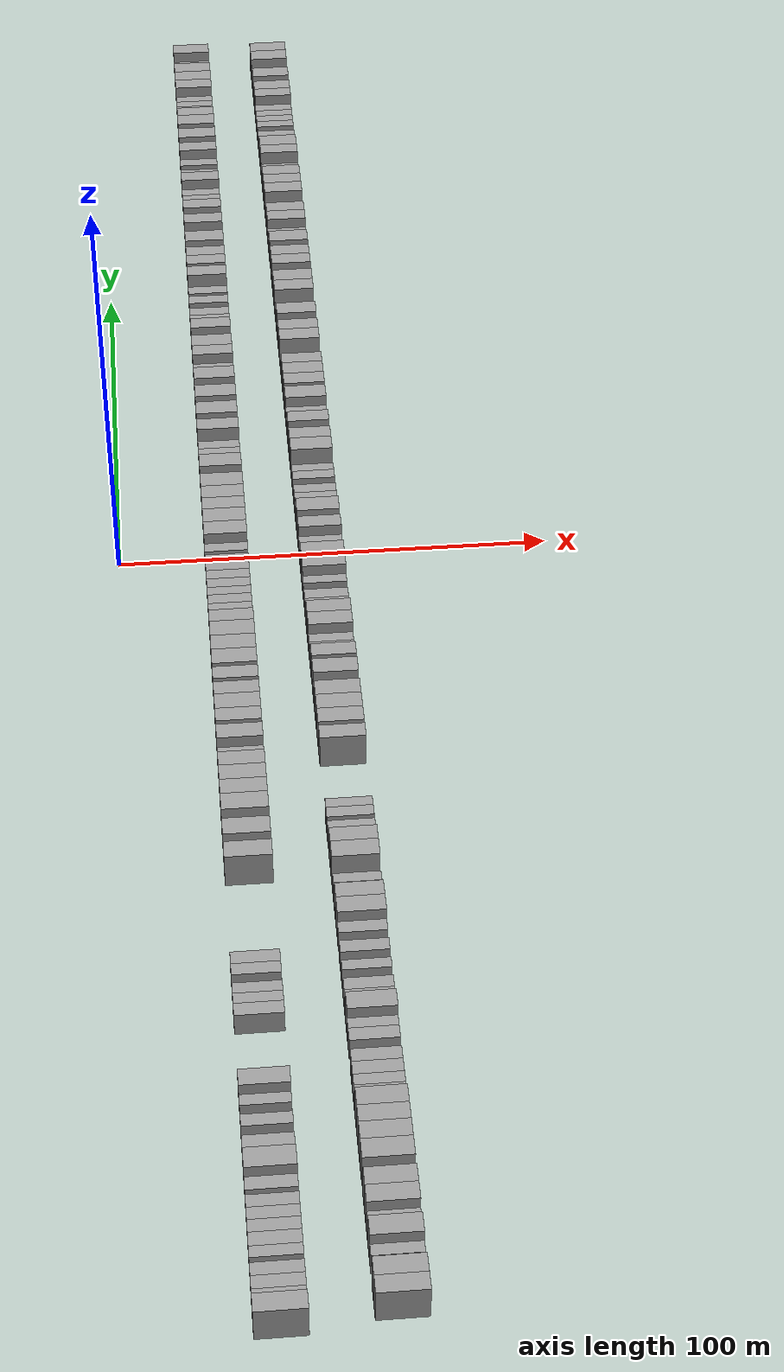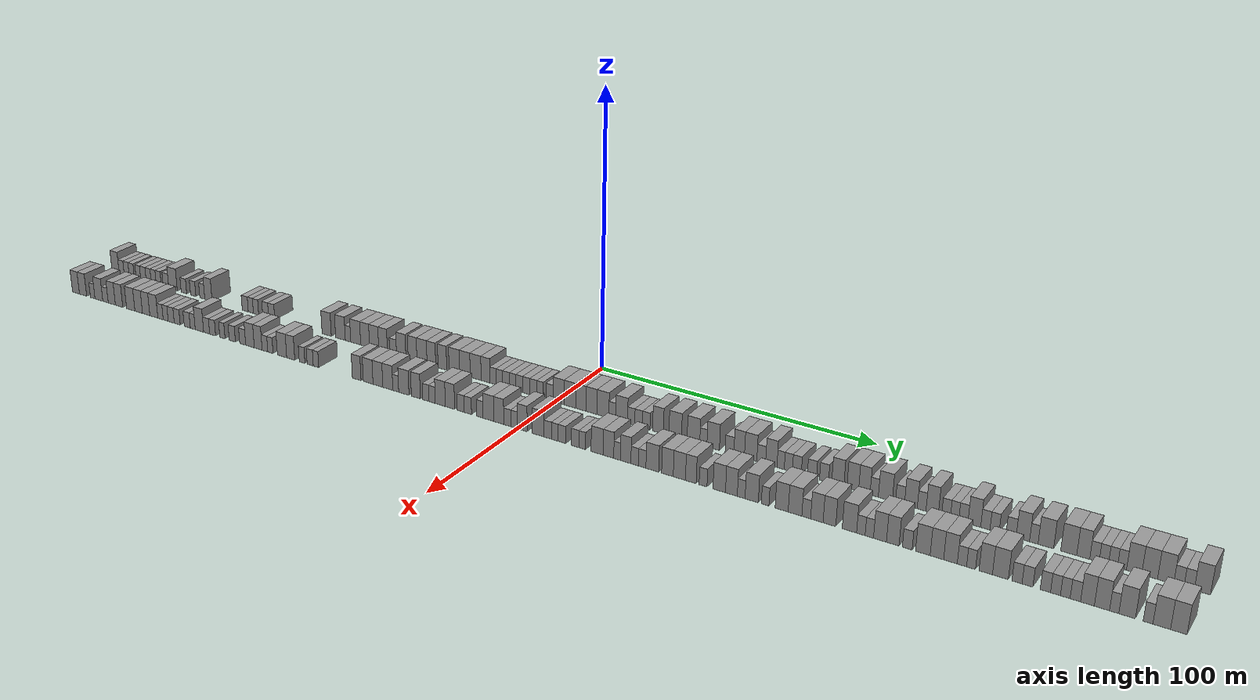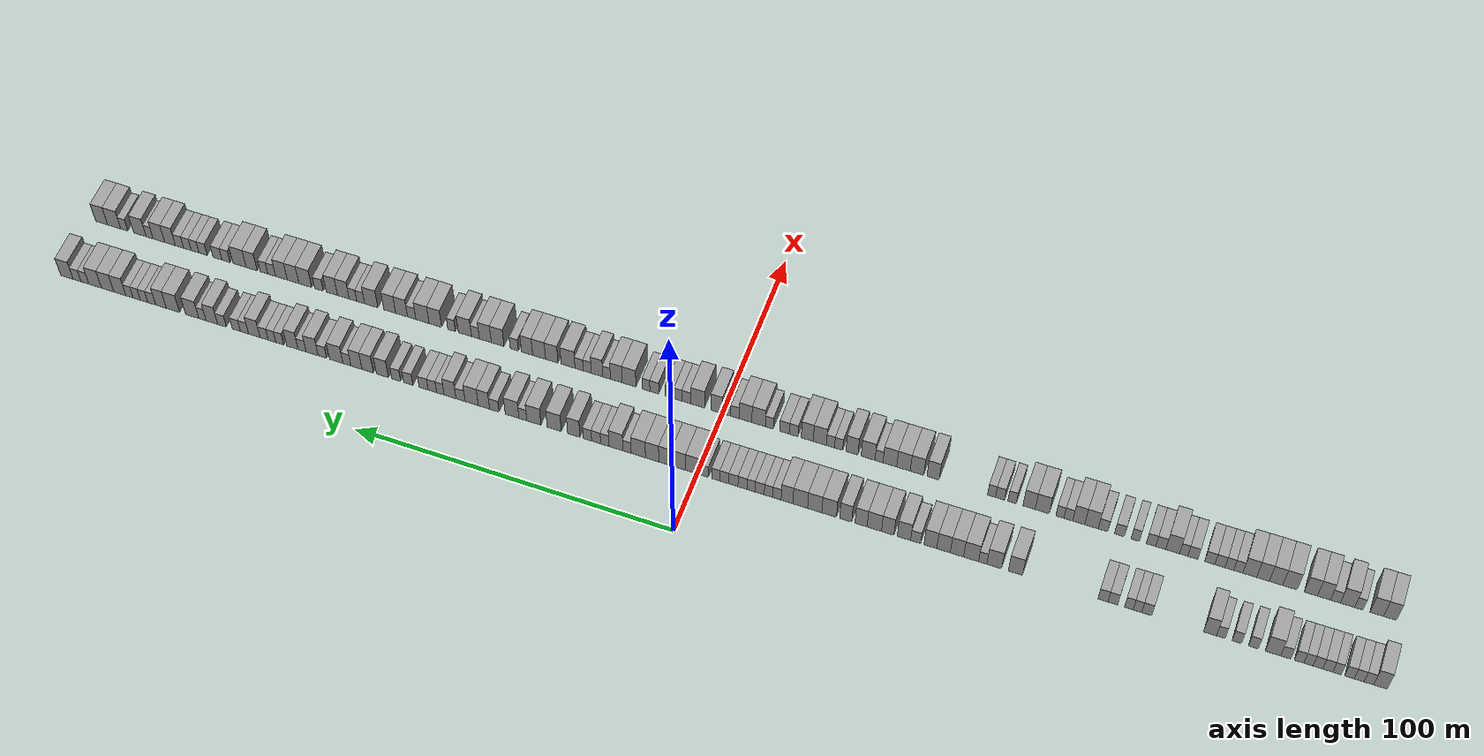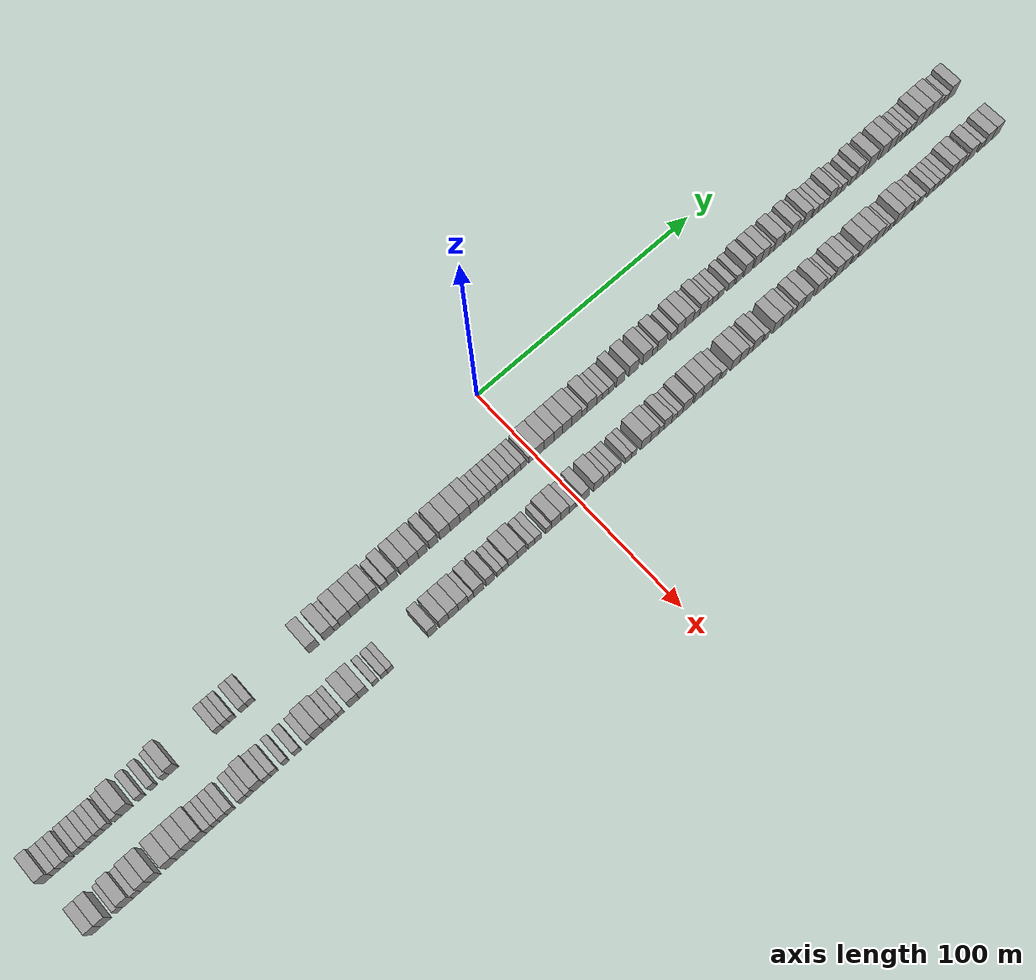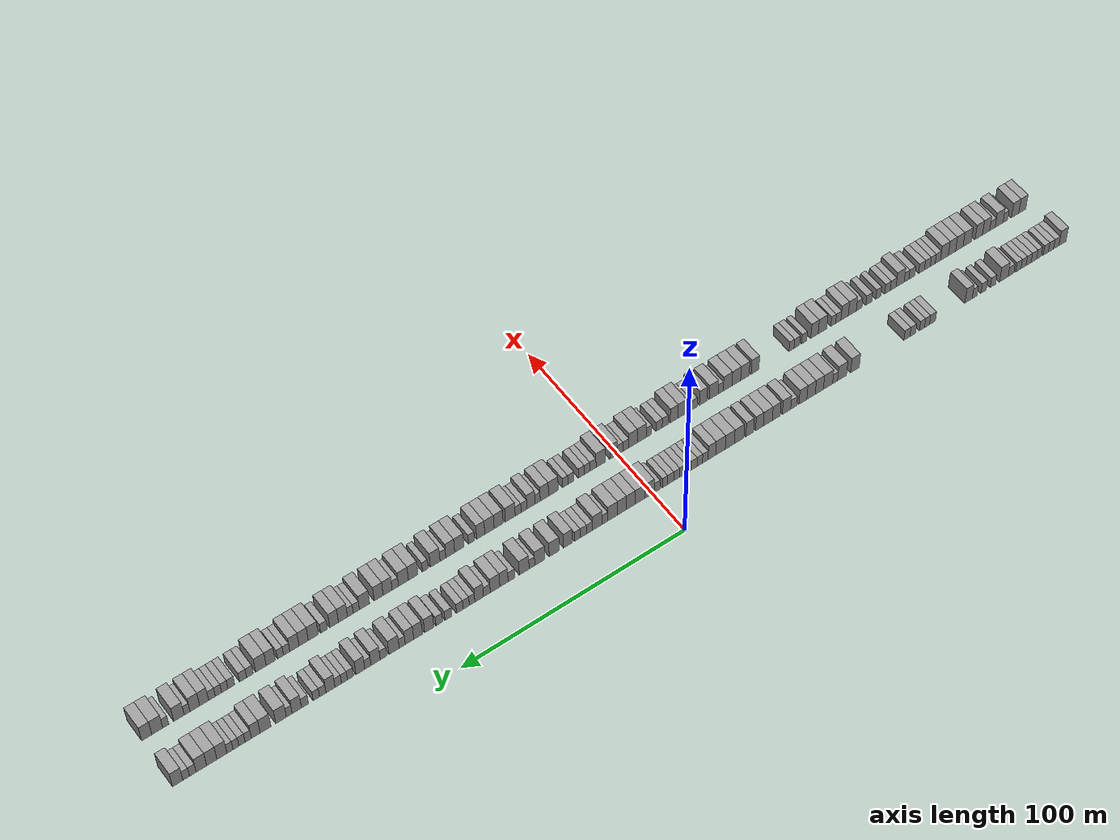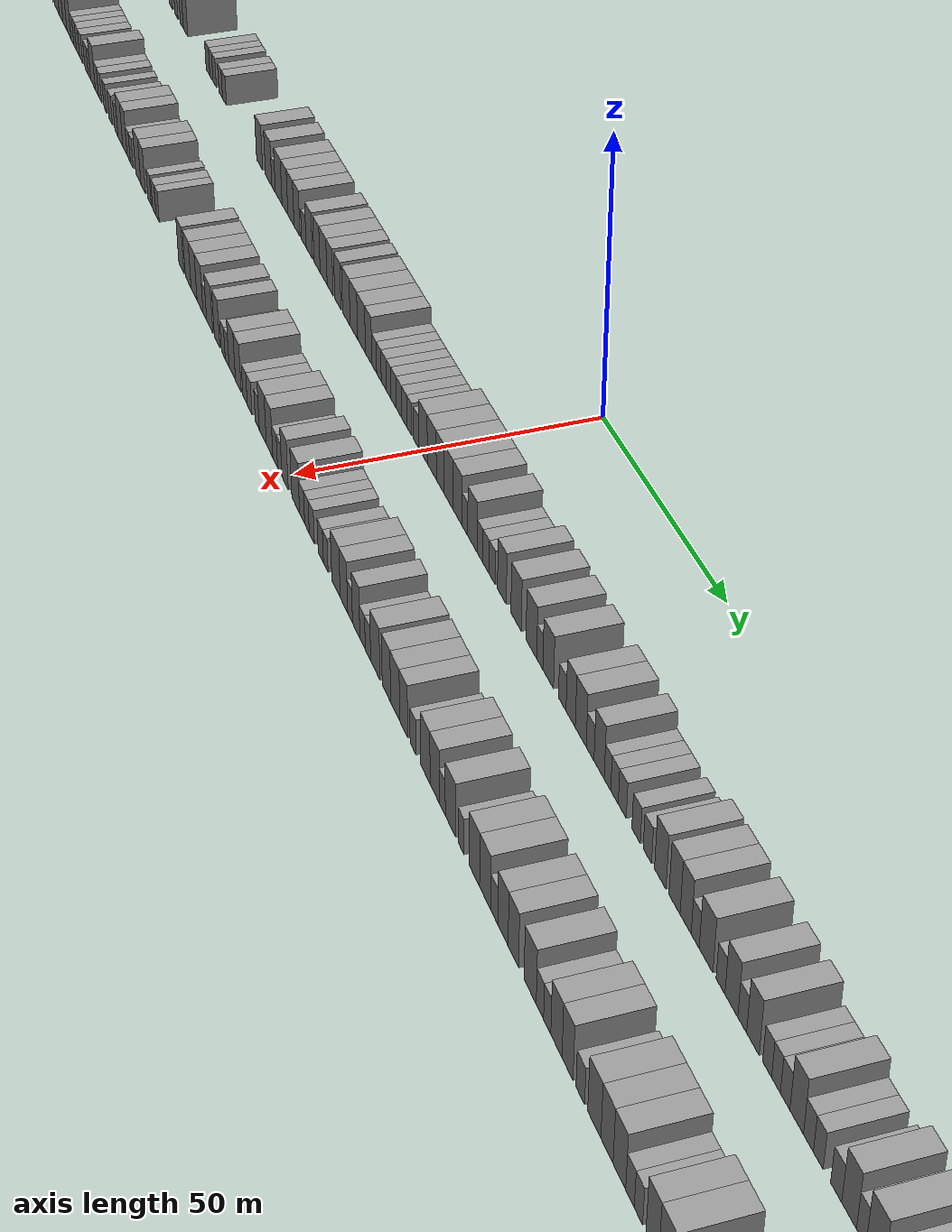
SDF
<sdf version="1.6">
 <world name="default">
  <scene>
   <sky><clouds><speed>12</speed></clouds></sky>
   <ambient>0.4 0.4 0.4 1</ambient>
   <background>0.7 0.7 0.7 1</background>
   <shadows>1</shadows>
  </scene>
  <gravity>0 0 -9.8066</gravity>
  <magnetic_field>6e-06 2.3e-05 -4.2e-05</magnetic_field>
  <physics default="0" name="default_physics" type="ode">
   <ode>
    <solver>
     <type>quick</type>
     <iters>10</iters>
     <sor>1.0</sor>
     <use_dynamic_moi_rescaling>0</use_dynamic_moi_rescaling>
    </solver>
    <constraints>
     <cfm>0</cfm>
     <erp>0.2</erp>
     <contact_max_correcting_vel>100</contact_max_correcting_vel>
     <contact_surface_layer>0.001</contact_surface_layer>
    </constraints>
   </ode>
   <max_step_size>0.004</max_step_size>
   <real_time_factor>1</real_time_factor>
   <real_time_update_rate>250</real_time_update_rate>
  </physics>
  <light name="sun" type="directional">
   <pose>0 0 10 0 0 0</pose>
   <diffuse>0.8 0.8 0.8 1</diffuse>
   <specular>0.2 0.2 0.2 1</specular>
   <attenuation>
    <range>1000</range>
    <constant>0.9</constant>
    <linear>0.01</linear>
    <quadratic>0.001</quadratic>
   </attenuation>
   <direction>-0.5 0.1 -0.9</direction>
  </light>
  <model name="building_1">
   <static>1</static>
   <pose>25.0000 -202.0835 0 0.000000 0.000000 0.000000</pose>
   <link name="link">
    <pose>0 0 4.50 0 0 0</pose>
    <collision name="collision"><geometry><box><size>10.0000 3.8331 9.0000</size></box></geometry></collision>
    <visual name="visual">
     <cast_shadows>0</cast_shadows>
     <geometry><box><size>10.0000 3.8331 9.0000</size></box></geometry>
     <material>
      <script>
       <uri>model://grey_wall/materials/scripts</uri>
       <uri>model://grey_wall/materials/textures</uri>
       <name>vrc/grey_wall</name>
      </script>
     </material>
    </visual>
   </link>
  </model>
  <model name="building_2">
   <static>1</static>
   <pose>25.0000 -198.8063 0 0.000000 0.000000 0.000000</pose>
   <link name="link">
    <pose>0 0 3.00 0 0 0</pose>
    <collision name="collision"><geometry><box><size>10.0000 2.7212 6.0000</size></box></geometry></collision>
    <visual name="visual">
     <cast_shadows>0</cast_shadows>
     <geometry><box><size>10.0000 2.7212 6.0000</size></box></geometry>
     <material>
      <script>
       <uri>model://grey_wall/materials/scripts</uri>
       <uri>model://grey_wall/materials/textures</uri>
       <name>vrc/grey_wall</name>
      </script>
     </material>
    </visual>
   </link>
  </model>
  <model name="building_3">
   <static>1</static>
   <pose>25.0000 -196.0775 0 0.000000 0.000000 0.000000</pose>
   <link name="link">
    <pose>0 0 3.00 0 0 0</pose>
    <collision name="collision"><geometry><box><size>10.0000 2.7364 6.0000</size></box></geometry></collision>
    <visual name="visual">
     <cast_shadows>0</cast_shadows>
     <geometry><box><size>10.0000 2.7364 6.0000</size></box></geometry>
     <material>
      <script>
       <uri>model://grey_wall/materials/scripts</uri>
       <uri>model://grey_wall/materials/textures</uri>
       <name>vrc/grey_wall</name>
      </script>
     </material>
    </visual>
   </link>
  </model>
  <model name="building_4">
   <static>1</static>
   <pose>25.0000 -193.3629 0 0.000000 0.000000 0.000000</pose>
   <link name="link">
    <pose>0 0 3.00 0 0 0</pose>
    <collision name="collision"><geometry><box><size>10.0000 2.6928 6.0000</size></box></geometry></collision>
    <visual name="visual">
     <cast_shadows>0</cast_shadows>
     <geometry><box><size>10.0000 2.6928 6.0000</size></box></geometry>
     <material>
      <script>
       <uri>model://grey_wall/materials/scripts</uri>
       <uri>model://grey_wall/materials/textures</uri>
       <name>vrc/grey_wall</name>
      </script>
     </material>
    </visual>
   </link>
  </model>
  <model name="building_5">
   <static>1</static>
   <pose>25.0000 -189.8049 0 0.000000 0.000000 0.000000</pose>
   <link name="link">
    <pose>0 0 3.00 0 0 0</pose>
    <collision name="collision"><geometry><box><size>10.0000 2.4231 6.0000</size></box></geometry></collision>
    <visual name="visual">
     <cast_shadows>0</cast_shadows>
     <geometry><box><size>10.0000 2.4231 6.0000</size></box></geometry>
     <material>
      <script>
       <uri>model://grey_wall/materials/scripts</uri>
       <uri>model://grey_wall/materials/textures</uri>
       <name>vrc/grey_wall</name>
      </script>
     </material>
    </visual>
   </link>
  </model>
  <model name="building_6">
   <static>1</static>
   <pose>25.0000 -187.1418 0 0.000000 0.000000 0.000000</pose>
   <link name="link">
    <pose>0 0 3.00 0 0 0</pose>
    <collision name="collision"><geometry><box><size>10.0000 2.9031 6.0000</size></box></geometry></collision>
    <visual name="visual">
     <cast_shadows>0</cast_shadows>
     <geometry><box><size>10.0000 2.9031 6.0000</size></box></geometry>
     <material>
      <script>
       <uri>model://grey_wall/materials/scripts</uri>
       <uri>model://grey_wall/materials/textures</uri>
       <name>vrc/grey_wall</name>
      </script>
     </material>
    </visual>
   </link>
  </model>
  <model name="building_7">
   <static>1</static>
   <pose>25.0000 -184.3537 0 0.000000 0.000000 0.000000</pose>
   <link name="link">
    <pose>0 0 3.00 0 0 0</pose>
    <collision name="collision"><geometry><box><size>10.0000 2.6732 6.0000</size></box></geometry></collision>
    <visual name="visual">
     <cast_shadows>0</cast_shadows>
     <geometry><box><size>10.0000 2.6732 6.0000</size></box></geometry>
     <material>
      <script>
       <uri>model://grey_wall/materials/scripts</uri>
       <uri>model://grey_wall/materials/textures</uri>
       <name>vrc/grey_wall</name>
      </script>
     </material>
    </visual>
   </link>
  </model>
  <model name="building_8">
   <static>1</static>
   <pose>25.0000 -181.7031 0 0.000000 0.000000 0.000000</pose>
   <link name="link">
    <pose>0 0 3.00 0 0 0</pose>
    <collision name="collision"><geometry><box><size>10.0000 2.6281 6.0000</size></box></geometry></collision>
    <visual name="visual">
     <cast_shadows>0</cast_shadows>
     <geometry><box><size>10.0000 2.6281 6.0000</size></box></geometry>
     <material>
      <script>
       <uri>model://grey_wall/materials/scripts</uri>
       <uri>model://grey_wall/materials/textures</uri>
       <name>vrc/grey_wall</name>
      </script>
     </material>
    </visual>
   </link>
  </model>
  <model name="building_9">
   <static>1</static>
   <pose>25.0000 -179.0499 0 0.000000 0.000000 0.000000</pose>
   <link name="link">
    <pose>0 0 3.00 0 0 0</pose>
    <collision name="collision"><geometry><box><size>10.0000 2.6783 6.0000</size></box></geometry></collision>
    <visual name="visual">
     <cast_shadows>0</cast_shadows>
     <geometry><box><size>10.0000 2.6783 6.0000</size></box></geometry>
     <material>
      <script>
       <uri>model://grey_wall/materials/scripts</uri>
       <uri>model://grey_wall/materials/textures</uri>
       <name>vrc/grey_wall</name>
      </script>
     </material>
    </visual>
   </link>
  </model>
  <model name="building_10">
   <static>1</static>
   <pose>25.0000 -175.2696 0 0.000000 0.000000 0.000000</pose>
   <link name="link">
    <pose>0 0 3.00 0 0 0</pose>
    <collision name="collision"><geometry><box><size>10.0000 2.8823 6.0000</size></box></geometry></collision>
    <visual name="visual">
     <cast_shadows>0</cast_shadows>
     <geometry><box><size>10.0000 2.8823 6.0000</size></box></geometry>
     <material>
      <script>
       <uri>model://grey_wall/materials/scripts</uri>
       <uri>model://grey_wall/materials/textures</uri>
       <name>vrc/grey_wall</name>
      </script>
     </material>
    </visual>
   </link>
  </model>
  <model name="building_11">
   <static>1</static>
   <pose>25.0000 -171.6213 0 0.000000 0.000000 0.000000</pose>
   <link name="link">
    <pose>0 0 4.50 0 0 0</pose>
    <collision name="collision"><geometry><box><size>10.0000 4.4142 9.0000</size></box></geometry></collision>
    <visual name="visual">
     <cast_shadows>0</cast_shadows>
     <geometry><box><size>10.0000 4.4142 9.0000</size></box></geometry>
     <material>
      <script>
       <uri>model://grey_wall/materials/scripts</uri>
       <uri>model://grey_wall/materials/textures</uri>
       <name>vrc/grey_wall</name>
      </script>
     </material>
    </visual>
   </link>
  </model>
  <model name="building_12">
   <static>1</static>
   <pose>25.0000 -166.0089 0 0.000000 0.000000 0.000000</pose>
   <link name="link">
    <pose>0 0 3.00 0 0 0</pose>
    <collision name="collision"><geometry><box><size>10.0000 2.8105 6.0000</size></box></geometry></collision>
    <visual name="visual">
     <cast_shadows>0</cast_shadows>
     <geometry><box><size>10.0000 2.8105 6.0000</size></box></geometry>
     <material>
      <script>
       <uri>model://grey_wall/materials/scripts</uri>
       <uri>model://grey_wall/materials/textures</uri>
       <name>vrc/grey_wall</name>
      </script>
     </material>
    </visual>
   </link>
  </model>
  <model name="building_13">
   <static>1</static>
   <pose>25.0000 -161.2467 0 0.000000 0.000000 0.000000</pose>
   <link name="link">
    <pose>0 0 3.00 0 0 0</pose>
    <collision name="collision"><geometry><box><size>10.0000 2.7138 6.0000</size></box></geometry></collision>
    <visual name="visual">
     <cast_shadows>0</cast_shadows>
     <geometry><box><size>10.0000 2.7138 6.0000</size></box></geometry>
     <material>
      <script>
       <uri>model://grey_wall/materials/scripts</uri>
       <uri>model://grey_wall/materials/textures</uri>
       <name>vrc/grey_wall</name>
      </script>
     </material>
    </visual>
   </link>
  </model>
  <model name="building_14">
   <static>1</static>
   <pose>25.0000 -156.6414 0 0.000000 0.000000 0.000000</pose>
   <link name="link">
    <pose>0 0 3.00 0 0 0</pose>
    <collision name="collision"><geometry><box><size>10.0000 2.4969 6.0000</size></box></geometry></collision>
    <visual name="visual">
     <cast_shadows>0</cast_shadows>
     <geometry><box><size>10.0000 2.4969 6.0000</size></box></geometry>
     <material>
      <script>
       <uri>model://grey_wall/materials/scripts</uri>
       <uri>model://grey_wall/materials/textures</uri>
       <name>vrc/grey_wall</name>
      </script>
     </material>
    </visual>
   </link>
  </model>
  <model name="building_15">
   <static>1</static>
   <pose>25.0000 -153.5382 0 0.000000 0.000000 0.000000</pose>
   <link name="link">
    <pose>0 0 4.50 0 0 0</pose>
    <collision name="collision"><geometry><box><size>10.0000 3.7095 9.0000</size></box></geometry></collision>
    <visual name="visual">
     <cast_shadows>0</cast_shadows>
     <geometry><box><size>10.0000 3.7095 9.0000</size></box></geometry>
     <material>
      <script>
       <uri>model://grey_wall/materials/scripts</uri>
       <uri>model://grey_wall/materials/textures</uri>
       <name>vrc/grey_wall</name>
      </script>
     </material>
    </visual>
   </link>
  </model>
  <model name="building_16">
   <static>1</static>
   <pose>25.0000 -135.2273 0 0.000000 0.000000 0.000000</pose>
   <link name="link">
    <pose>0 0 3.00 0 0 0</pose>
    <collision name="collision"><geometry><box><size>10.0000 2.9708 6.0000</size></box></geometry></collision>
    <visual name="visual">
     <cast_shadows>0</cast_shadows>
     <geometry><box><size>10.0000 2.9708 6.0000</size></box></geometry>
     <material>
      <script>
       <uri>model://grey_wall/materials/scripts</uri>
       <uri>model://grey_wall/materials/textures</uri>
       <name>vrc/grey_wall</name>
      </script>
     </material>
    </visual>
   </link>
  </model>
  <model name="building_17">
   <static>1</static>
   <pose>25.0000 -132.5023 0 0.000000 0.000000 0.000000</pose>
   <link name="link">
    <pose>0 0 3.00 0 0 0</pose>
    <collision name="collision"><geometry><box><size>10.0000 2.4791 6.0000</size></box></geometry></collision>
    <visual name="visual">
     <cast_shadows>0</cast_shadows>
     <geometry><box><size>10.0000 2.4791 6.0000</size></box></geometry>
     <material>
      <script>
       <uri>model://grey_wall/materials/scripts</uri>
       <uri>model://grey_wall/materials/textures</uri>
       <name>vrc/grey_wall</name>
      </script>
     </material>
    </visual>
   </link>
  </model>
  <model name="building_18">
   <static>1</static>
   <pose>25.0000 -129.9862 0 0.000000 0.000000 0.000000</pose>
   <link name="link">
    <pose>0 0 3.00 0 0 0</pose>
    <collision name="collision"><geometry><box><size>10.0000 2.5531 6.0000</size></box></geometry></collision>
    <visual name="visual">
     <cast_shadows>0</cast_shadows>
     <geometry><box><size>10.0000 2.5531 6.0000</size></box></geometry>
     <material>
      <script>
       <uri>model://grey_wall/materials/scripts</uri>
       <uri>model://grey_wall/materials/textures</uri>
       <name>vrc/grey_wall</name>
      </script>
     </material>
    </visual>
   </link>
  </model>
  <model name="building_19">
   <static>1</static>
   <pose>25.0000 -125.3027 0 0.000000 0.000000 0.000000</pose>
   <link name="link">
    <pose>0 0 3.00 0 0 0</pose>
    <collision name="collision"><geometry><box><size>10.0000 2.8138 6.0000</size></box></geometry></collision>
    <visual name="visual">
     <cast_shadows>0</cast_shadows>
     <geometry><box><size>10.0000 2.8138 6.0000</size></box></geometry>
     <material>
      <script>
       <uri>model://grey_wall/materials/scripts</uri>
       <uri>model://grey_wall/materials/textures</uri>
       <name>vrc/grey_wall</name>
      </script>
     </material>
    </visual>
   </link>
  </model>
  <model name="building_20">
   <static>1</static>
   <pose>25.0000 -122.4214 0 0.000000 0.000000 0.000000</pose>
   <link name="link">
    <pose>0 0 3.00 0 0 0</pose>
    <collision name="collision"><geometry><box><size>10.0000 2.9488 6.0000</size></box></geometry></collision>
    <visual name="visual">
     <cast_shadows>0</cast_shadows>
     <geometry><box><size>10.0000 2.9488 6.0000</size></box></geometry>
     <material>
      <script>
       <uri>model://grey_wall/materials/scripts</uri>
       <uri>model://grey_wall/materials/textures</uri>
       <name>vrc/grey_wall</name>
      </script>
     </material>
    </visual>
   </link>
  </model>
  <model name="building_21">
   <static>1</static>
   <pose>25.0000 -96.5870 0 0.000000 0.000000 0.000000</pose>
   <link name="link">
    <pose>0 0 4.50 0 0 0</pose>
    <collision name="collision"><geometry><box><size>10.0000 4.2400 9.0000</size></box></geometry></collision>
    <visual name="visual">
     <cast_shadows>0</cast_shadows>
     <geometry><box><size>10.0000 4.2400 9.0000</size></box></geometry>
     <material>
      <script>
       <uri>model://grey_wall/materials/scripts</uri>
       <uri>model://grey_wall/materials/textures</uri>
       <name>vrc/grey_wall</name>
      </script>
     </material>
    </visual>
   </link>
  </model>
  <model name="building_22">
   <static>1</static>
   <pose>25.0000 -90.2706 0 0.000000 0.000000 0.000000</pose>
   <link name="link">
    <pose>0 0 4.50 0 0 0</pose>
    <collision name="collision"><geometry><box><size>10.0000 4.3928 9.0000</size></box></geometry></collision>
    <visual name="visual">
     <cast_shadows>0</cast_shadows>
     <geometry><box><size>10.0000 4.3928 9.0000</size></box></geometry>
     <material>
      <script>
       <uri>model://grey_wall/materials/scripts</uri>
       <uri>model://grey_wall/materials/textures</uri>
       <name>vrc/grey_wall</name>
      </script>
     </material>
    </visual>
   </link>
  </model>
  <model name="building_23">
   <static>1</static>
   <pose>25.0000 -86.8506 0 0.000000 0.000000 0.000000</pose>
   <link name="link">
    <pose>0 0 3.00 0 0 0</pose>
    <collision name="collision"><geometry><box><size>10.0000 2.4471 6.0000</size></box></geometry></collision>
    <visual name="visual">
     <cast_shadows>0</cast_shadows>
     <geometry><box><size>10.0000 2.4471 6.0000</size></box></geometry>
     <material>
      <script>
       <uri>model://grey_wall/materials/scripts</uri>
       <uri>model://grey_wall/materials/textures</uri>
       <name>vrc/grey_wall</name>
      </script>
     </material>
    </visual>
   </link>
  </model>
  <model name="building_24">
   <static>1</static>
   <pose>25.0000 -83.3919 0 0.000000 0.000000 0.000000</pose>
   <link name="link">
    <pose>0 0 4.50 0 0 0</pose>
    <collision name="collision"><geometry><box><size>10.0000 4.4703 9.0000</size></box></geometry></collision>
    <visual name="visual">
     <cast_shadows>0</cast_shadows>
     <geometry><box><size>10.0000 4.4703 9.0000</size></box></geometry>
     <material>
      <script>
       <uri>model://grey_wall/materials/scripts</uri>
       <uri>model://grey_wall/materials/textures</uri>
       <name>vrc/grey_wall</name>
      </script>
     </material>
    </visual>
   </link>
  </model>
  <model name="building_25">
   <static>1</static>
   <pose>25.0000 -79.1660 0 0.000000 0.000000 0.000000</pose>
   <link name="link">
    <pose>0 0 4.50 0 0 0</pose>
    <collision name="collision"><geometry><box><size>10.0000 3.9814 9.0000</size></box></geometry></collision>
    <visual name="visual">
     <cast_shadows>0</cast_shadows>
     <geometry><box><size>10.0000 3.9814 9.0000</size></box></geometry>
     <material>
      <script>
       <uri>model://grey_wall/materials/scripts</uri>
       <uri>model://grey_wall/materials/textures</uri>
       <name>vrc/grey_wall</name>
      </script>
     </material>
    </visual>
   </link>
  </model>
  <model name="building_26">
   <static>1</static>
   <pose>25.0000 -75.1473 0 0.000000 0.000000 0.000000</pose>
   <link name="link">
    <pose>0 0 4.50 0 0 0</pose>
    <collision name="collision"><geometry><box><size>10.0000 4.0561 9.0000</size></box></geometry></collision>
    <visual name="visual">
     <cast_shadows>0</cast_shadows>
     <geometry><box><size>10.0000 4.0561 9.0000</size></box></geometry>
     <material>
      <script>
       <uri>model://grey_wall/materials/scripts</uri>
       <uri>model://grey_wall/materials/textures</uri>
       <name>vrc/grey_wall</name>
      </script>
     </material>
    </visual>
   </link>
  </model>
  <model name="building_27">
   <static>1</static>
   <pose>25.0000 -71.1980 0 0.000000 0.000000 0.000000</pose>
   <link name="link">
    <pose>0 0 4.50 0 0 0</pose>
    <collision name="collision"><geometry><box><size>10.0000 3.8425 9.0000</size></box></geometry></collision>
    <visual name="visual">
     <cast_shadows>0</cast_shadows>
     <geometry><box><size>10.0000 3.8425 9.0000</size></box></geometry>
     <material>
      <script>
       <uri>model://grey_wall/materials/scripts</uri>
       <uri>model://grey_wall/materials/textures</uri>
       <name>vrc/grey_wall</name>
      </script>
     </material>
    </visual>
   </link>
  </model>
  <model name="building_28">
   <static>1</static>
   <pose>25.0000 -66.7811 0 0.000000 0.000000 0.000000</pose>
   <link name="link">
    <pose>0 0 3.00 0 0 0</pose>
    <collision name="collision"><geometry><box><size>10.0000 2.9913 6.0000</size></box></geometry></collision>
    <visual name="visual">
     <cast_shadows>0</cast_shadows>
     <geometry><box><size>10.0000 2.9913 6.0000</size></box></geometry>
     <material>
      <script>
       <uri>model://grey_wall/materials/scripts</uri>
       <uri>model://grey_wall/materials/textures</uri>
       <name>vrc/grey_wall</name>
      </script>
     </material>
    </visual>
   </link>
  </model>
  <model name="building_29">
   <static>1</static>
   <pose>25.0000 -63.2597 0 0.000000 0.000000 0.000000</pose>
   <link name="link">
    <pose>0 0 4.50 0 0 0</pose>
    <collision name="collision"><geometry><box><size>10.0000 4.0516 9.0000</size></box></geometry></collision>
    <visual name="visual">
     <cast_shadows>0</cast_shadows>
     <geometry><box><size>10.0000 4.0516 9.0000</size></box></geometry>
     <material>
      <script>
       <uri>model://grey_wall/materials/scripts</uri>
       <uri>model://grey_wall/materials/textures</uri>
       <name>vrc/grey_wall</name>
      </script>
     </material>
    </visual>
   </link>
  </model>
  <model name="building_30">
   <static>1</static>
   <pose>25.0000 -58.3479 0 0.000000 0.000000 0.000000</pose>
   <link name="link">
    <pose>0 0 4.50 0 0 0</pose>
    <collision name="collision"><geometry><box><size>10.0000 3.7719 9.0000</size></box></geometry></collision>
    <visual name="visual">
     <cast_shadows>0</cast_shadows>
     <geometry><box><size>10.0000 3.7719 9.0000</size></box></geometry>
     <material>
      <script>
       <uri>model://grey_wall/materials/scripts</uri>
       <uri>model://grey_wall/materials/textures</uri>
       <name>vrc/grey_wall</name>
      </script>
     </material>
    </visual>
   </link>
  </model>
  <model name="building_31">
   <static>1</static>
   <pose>25.0000 -54.2955 0 0.000000 0.000000 0.000000</pose>
   <link name="link">
    <pose>0 0 4.50 0 0 0</pose>
    <collision name="collision"><geometry><box><size>10.0000 4.3330 9.0000</size></box></geometry></collision>
    <visual name="visual">
     <cast_shadows>0</cast_shadows>
     <geometry><box><size>10.0000 4.3330 9.0000</size></box></geometry>
     <material>
      <script>
       <uri>model://grey_wall/materials/scripts</uri>
       <uri>model://grey_wall/materials/textures</uri>
       <name>vrc/grey_wall</name>
      </script>
     </material>
    </visual>
   </link>
  </model>
  <model name="building_32">
   <static>1</static>
   <pose>25.0000 -50.2881 0 0.000000 0.000000 0.000000</pose>
   <link name="link">
    <pose>0 0 4.50 0 0 0</pose>
    <collision name="collision"><geometry><box><size>10.0000 3.6818 9.0000</size></box></geometry></collision>
    <visual name="visual">
     <cast_shadows>0</cast_shadows>
     <geometry><box><size>10.0000 3.6818 9.0000</size></box></geometry>
     <material>
      <script>
       <uri>model://grey_wall/materials/scripts</uri>
       <uri>model://grey_wall/materials/textures</uri>
       <name>vrc/grey_wall</name>
      </script>
     </material>
    </visual>
   </link>
  </model>
  <model name="building_33">
   <static>1</static>
   <pose>25.0000 -45.6298 0 0.000000 0.000000 0.000000</pose>
   <link name="link">
    <pose>0 0 4.50 0 0 0</pose>
    <collision name="collision"><geometry><box><size>10.0000 3.6348 9.0000</size></box></geometry></collision>
    <visual name="visual">
     <cast_shadows>0</cast_shadows>
     <geometry><box><size>10.0000 3.6348 9.0000</size></box></geometry>
     <material>
      <script>
       <uri>model://grey_wall/materials/scripts</uri>
       <uri>model://grey_wall/materials/textures</uri>
       <name>vrc/grey_wall</name>
      </script>
     </material>
    </visual>
   </link>
  </model>
  <model name="building_34">
   <static>1</static>
   <pose>25.0000 -40.5821 0 0.000000 0.000000 0.000000</pose>
   <link name="link">
    <pose>0 0 4.50 0 0 0</pose>
    <collision name="collision"><geometry><box><size>10.0000 4.4606 9.0000</size></box></geometry></collision>
    <visual name="visual">
     <cast_shadows>0</cast_shadows>
     <geometry><box><size>10.0000 4.4606 9.0000</size></box></geometry>
     <material>
      <script>
       <uri>model://grey_wall/materials/scripts</uri>
       <uri>model://grey_wall/materials/textures</uri>
       <name>vrc/grey_wall</name>
      </script>
     </material>
    </visual>
   </link>
  </model>
  <model name="building_35">
   <static>1</static>
   <pose>25.0000 -36.1830 0 0.000000 0.000000 0.000000</pose>
   <link name="link">
    <pose>0 0 4.50 0 0 0</pose>
    <collision name="collision"><geometry><box><size>10.0000 4.3375 9.0000</size></box></geometry></collision>
    <visual name="visual">
     <cast_shadows>0</cast_shadows>
     <geometry><box><size>10.0000 4.3375 9.0000</size></box></geometry>
     <material>
      <script>
       <uri>model://grey_wall/materials/scripts</uri>
       <uri>model://grey_wall/materials/textures</uri>
       <name>vrc/grey_wall</name>
      </script>
     </material>
    </visual>
   </link>
  </model>
  <model name="building_36">
   <static>1</static>
   <pose>25.0000 -31.7675 0 0.000000 0.000000 0.000000</pose>
   <link name="link">
    <pose>0 0 4.50 0 0 0</pose>
    <collision name="collision"><geometry><box><size>10.0000 4.4934 9.0000</size></box></geometry></collision>
    <visual name="visual">
     <cast_shadows>0</cast_shadows>
     <geometry><box><size>10.0000 4.4934 9.0000</size></box></geometry>
     <material>
      <script>
       <uri>model://grey_wall/materials/scripts</uri>
       <uri>model://grey_wall/materials/textures</uri>
       <name>vrc/grey_wall</name>
      </script>
     </material>
    </visual>
   </link>
  </model>
  <model name="building_37">
   <static>1</static>
   <pose>25.0000 -27.7102 0 0.000000 0.000000 0.000000</pose>
   <link name="link">
    <pose>0 0 4.50 0 0 0</pose>
    <collision name="collision"><geometry><box><size>10.0000 3.6212 9.0000</size></box></geometry></collision>
    <visual name="visual">
     <cast_shadows>0</cast_shadows>
     <geometry><box><size>10.0000 3.6212 9.0000</size></box></geometry>
     <material>
      <script>
       <uri>model://grey_wall/materials/scripts</uri>
       <uri>model://grey_wall/materials/textures</uri>
       <name>vrc/grey_wall</name>
      </script>
     </material>
    </visual>
   </link>
  </model>
  <model name="building_38">
   <static>1</static>
   <pose>25.0000 -24.5940 0 0.000000 0.000000 0.000000</pose>
   <link name="link">
    <pose>0 0 3.00 0 0 0</pose>
    <collision name="collision"><geometry><box><size>10.0000 2.6112 6.0000</size></box></geometry></collision>
    <visual name="visual">
     <cast_shadows>0</cast_shadows>
     <geometry><box><size>10.0000 2.6112 6.0000</size></box></geometry>
     <material>
      <script>
       <uri>model://grey_wall/materials/scripts</uri>
       <uri>model://grey_wall/materials/textures</uri>
       <name>vrc/grey_wall</name>
      </script>
     </material>
    </visual>
   </link>
  </model>
  <model name="building_39">
   <static>1</static>
   <pose>25.0000 -22.0062 0 0.000000 0.000000 0.000000</pose>
   <link name="link">
    <pose>0 0 3.00 0 0 0</pose>
    <collision name="collision"><geometry><box><size>10.0000 2.5643 6.0000</size></box></geometry></collision>
    <visual name="visual">
     <cast_shadows>0</cast_shadows>
     <geometry><box><size>10.0000 2.5643 6.0000</size></box></geometry>
     <material>
      <script>
       <uri>model://grey_wall/materials/scripts</uri>
       <uri>model://grey_wall/materials/textures</uri>
       <name>vrc/grey_wall</name>
      </script>
     </material>
    </visual>
   </link>
  </model>
  <model name="building_40">
   <static>1</static>
   <pose>25.0000 -19.3126 0 0.000000 0.000000 0.000000</pose>
   <link name="link">
    <pose>0 0 3.00 0 0 0</pose>
    <collision name="collision"><geometry><box><size>10.0000 2.8229 6.0000</size></box></geometry></collision>
    <visual name="visual">
     <cast_shadows>0</cast_shadows>
     <geometry><box><size>10.0000 2.8229 6.0000</size></box></geometry>
     <material>
      <script>
       <uri>model://grey_wall/materials/scripts</uri>
       <uri>model://grey_wall/materials/textures</uri>
       <name>vrc/grey_wall</name>
      </script>
     </material>
    </visual>
   </link>
  </model>
  <model name="building_41">
   <static>1</static>
   <pose>25.0000 -16.6580 0 0.000000 0.000000 0.000000</pose>
   <link name="link">
    <pose>0 0 3.00 0 0 0</pose>
    <collision name="collision"><geometry><box><size>10.0000 2.4863 6.0000</size></box></geometry></collision>
    <visual name="visual">
     <cast_shadows>0</cast_shadows>
     <geometry><box><size>10.0000 2.4863 6.0000</size></box></geometry>
     <material>
      <script>
       <uri>model://grey_wall/materials/scripts</uri>
       <uri>model://grey_wall/materials/textures</uri>
       <name>vrc/grey_wall</name>
      </script>
     </material>
    </visual>
   </link>
  </model>
  <model name="building_42">
   <static>1</static>
   <pose>25.0000 -14.0102 0 0.000000 0.000000 0.000000</pose>
   <link name="link">
    <pose>0 0 3.00 0 0 0</pose>
    <collision name="collision"><geometry><box><size>10.0000 2.8092 6.0000</size></box></geometry></collision>
    <visual name="visual">
     <cast_shadows>0</cast_shadows>
     <geometry><box><size>10.0000 2.8092 6.0000</size></box></geometry>
     <material>
      <script>
       <uri>model://grey_wall/materials/scripts</uri>
       <uri>model://grey_wall/materials/textures</uri>
       <name>vrc/grey_wall</name>
      </script>
     </material>
    </visual>
   </link>
  </model>
  <model name="building_43">
   <static>1</static>
   <pose>25.0000 -11.2068 0 0.000000 0.000000 0.000000</pose>
   <link name="link">
    <pose>0 0 3.00 0 0 0</pose>
    <collision name="collision"><geometry><box><size>10.0000 2.7976 6.0000</size></box></geometry></collision>
    <visual name="visual">
     <cast_shadows>0</cast_shadows>
     <geometry><box><size>10.0000 2.7976 6.0000</size></box></geometry>
     <material>
      <script>
       <uri>model://grey_wall/materials/scripts</uri>
       <uri>model://grey_wall/materials/textures</uri>
       <name>vrc/grey_wall</name>
      </script>
     </material>
    </visual>
   </link>
  </model>
  <model name="building_44">
   <static>1</static>
   <pose>25.0000 -8.4107 0 0.000000 0.000000 0.000000</pose>
   <link name="link">
    <pose>0 0 3.00 0 0 0</pose>
    <collision name="collision"><geometry><box><size>10.0000 2.7947 6.0000</size></box></geometry></collision>
    <visual name="visual">
     <cast_shadows>0</cast_shadows>
     <geometry><box><size>10.0000 2.7947 6.0000</size></box></geometry>
     <material>
      <script>
       <uri>model://grey_wall/materials/scripts</uri>
       <uri>model://grey_wall/materials/textures</uri>
       <name>vrc/grey_wall</name>
      </script>
     </material>
    </visual>
   </link>
  </model>
  <model name="building_45">
   <static>1</static>
   <pose>25.0000 -5.7582 0 0.000000 0.000000 0.000000</pose>
   <link name="link">
    <pose>0 0 3.00 0 0 0</pose>
    <collision name="collision"><geometry><box><size>10.0000 2.5102 6.0000</size></box></geometry></collision>
    <visual name="visual">
     <cast_shadows>0</cast_shadows>
     <geometry><box><size>10.0000 2.5102 6.0000</size></box></geometry>
     <material>
      <script>
       <uri>model://grey_wall/materials/scripts</uri>
       <uri>model://grey_wall/materials/textures</uri>
       <name>vrc/grey_wall</name>
      </script>
     </material>
    </visual>
   </link>
  </model>
  <model name="building_46">
   <static>1</static>
   <pose>25.0000 -2.1338 0 0.000000 0.000000 0.000000</pose>
   <link name="link">
    <pose>0 0 3.00 0 0 0</pose>
    <collision name="collision"><geometry><box><size>10.0000 2.7386 6.0000</size></box></geometry></collision>
    <visual name="visual">
     <cast_shadows>0</cast_shadows>
     <geometry><box><size>10.0000 2.7386 6.0000</size></box></geometry>
     <material>
      <script>
       <uri>model://grey_wall/materials/scripts</uri>
       <uri>model://grey_wall/materials/textures</uri>
       <name>vrc/grey_wall</name>
      </script>
     </material>
    </visual>
   </link>
  </model>
  <model name="building_47">
   <static>1</static>
   <pose>25.0000 1.4138 0 0.000000 0.000000 0.000000</pose>
   <link name="link">
    <pose>0 0 4.50 0 0 0</pose>
    <collision name="collision"><geometry><box><size>10.0000 4.3567 9.0000</size></box></geometry></collision>
    <visual name="visual">
     <cast_shadows>0</cast_shadows>
     <geometry><box><size>10.0000 4.3567 9.0000</size></box></geometry>
     <material>
      <script>
       <uri>model://grey_wall/materials/scripts</uri>
       <uri>model://grey_wall/materials/textures</uri>
       <name>vrc/grey_wall</name>
      </script>
     </material>
    </visual>
   </link>
  </model>
  <model name="building_48">
   <static>1</static>
   <pose>25.0000 5.8222 0 0.000000 0.000000 0.000000</pose>
   <link name="link">
    <pose>0 0 4.50 0 0 0</pose>
    <collision name="collision"><geometry><box><size>10.0000 4.4599 9.0000</size></box></geometry></collision>
    <visual name="visual">
     <cast_shadows>0</cast_shadows>
     <geometry><box><size>10.0000 4.4599 9.0000</size></box></geometry>
     <material>
      <script>
       <uri>model://grey_wall/materials/scripts</uri>
       <uri>model://grey_wall/materials/textures</uri>
       <name>vrc/grey_wall</name>
      </script>
     </material>
    </visual>
   </link>
  </model>
  <model name="building_49">
   <static>1</static>
   <pose>25.0000 10.0087 0 0.000000 0.000000 0.000000</pose>
   <link name="link">
    <pose>0 0 4.50 0 0 0</pose>
    <collision name="collision"><geometry><box><size>10.0000 3.9131 9.0000</size></box></geometry></collision>
    <visual name="visual">
     <cast_shadows>0</cast_shadows>
     <geometry><box><size>10.0000 3.9131 9.0000</size></box></geometry>
     <material>
      <script>
       <uri>model://grey_wall/materials/scripts</uri>
       <uri>model://grey_wall/materials/textures</uri>
       <name>vrc/grey_wall</name>
      </script>
     </material>
    </visual>
   </link>
  </model>
  <model name="building_50">
   <static>1</static>
   <pose>25.0000 14.0520 0 0.000000 0.000000 0.000000</pose>
   <link name="link">
    <pose>0 0 4.50 0 0 0</pose>
    <collision name="collision"><geometry><box><size>10.0000 4.1734 9.0000</size></box></geometry></collision>
    <visual name="visual">
     <cast_shadows>0</cast_shadows>
     <geometry><box><size>10.0000 4.1734 9.0000</size></box></geometry>
     <material>
      <script>
       <uri>model://grey_wall/materials/scripts</uri>
       <uri>model://grey_wall/materials/textures</uri>
       <name>vrc/grey_wall</name>
      </script>
     </material>
    </visual>
   </link>
  </model>
  <model name="building_51">
   <static>1</static>
   <pose>25.0000 18.3818 0 0.000000 0.000000 0.000000</pose>
   <link name="link">
    <pose>0 0 4.50 0 0 0</pose>
    <collision name="collision"><geometry><box><size>10.0000 4.4863 9.0000</size></box></geometry></collision>
    <visual name="visual">
     <cast_shadows>0</cast_shadows>
     <geometry><box><size>10.0000 4.4863 9.0000</size></box></geometry>
     <material>
      <script>
       <uri>model://grey_wall/materials/scripts</uri>
       <uri>model://grey_wall/materials/textures</uri>
       <name>vrc/grey_wall</name>
      </script>
     </material>
    </visual>
   </link>
  </model>
  <model name="building_52">
   <static>1</static>
   <pose>25.0000 21.9062 0 0.000000 0.000000 0.000000</pose>
   <link name="link">
    <pose>0 0 3.00 0 0 0</pose>
    <collision name="collision"><geometry><box><size>10.0000 2.5625 6.0000</size></box></geometry></collision>
    <visual name="visual">
     <cast_shadows>0</cast_shadows>
     <geometry><box><size>10.0000 2.5625 6.0000</size></box></geometry>
     <material>
      <script>
       <uri>model://grey_wall/materials/scripts</uri>
       <uri>model://grey_wall/materials/textures</uri>
       <name>vrc/grey_wall</name>
      </script>
     </material>
    </visual>
   </link>
  </model>
  <model name="building_53">
   <static>1</static>
   <pose>25.0000 25.3795 0 0.000000 0.000000 0.000000</pose>
   <link name="link">
    <pose>0 0 4.50 0 0 0</pose>
    <collision name="collision"><geometry><box><size>10.0000 4.3841 9.0000</size></box></geometry></collision>
    <visual name="visual">
     <cast_shadows>0</cast_shadows>
     <geometry><box><size>10.0000 4.3841 9.0000</size></box></geometry>
     <material>
      <script>
       <uri>model://grey_wall/materials/scripts</uri>
       <uri>model://grey_wall/materials/textures</uri>
       <name>vrc/grey_wall</name>
      </script>
     </material>
    </visual>
   </link>
  </model>
  <model name="building_54">
   <static>1</static>
   <pose>25.0000 28.8932 0 0.000000 0.000000 0.000000</pose>
   <link name="link">
    <pose>0 0 3.00 0 0 0</pose>
    <collision name="collision"><geometry><box><size>10.0000 2.6431 6.0000</size></box></geometry></collision>
    <visual name="visual">
     <cast_shadows>0</cast_shadows>
     <geometry><box><size>10.0000 2.6431 6.0000</size></box></geometry>
     <material>
      <script>
       <uri>model://grey_wall/materials/scripts</uri>
       <uri>model://grey_wall/materials/textures</uri>
       <name>vrc/grey_wall</name>
      </script>
     </material>
    </visual>
   </link>
  </model>
  <model name="building_55">
   <static>1</static>
   <pose>25.0000 31.6414 0 0.000000 0.000000 0.000000</pose>
   <link name="link">
    <pose>0 0 3.00 0 0 0</pose>
    <collision name="collision"><geometry><box><size>10.0000 2.8534 6.0000</size></box></geometry></collision>
    <visual name="visual">
     <cast_shadows>0</cast_shadows>
     <geometry><box><size>10.0000 2.8534 6.0000</size></box></geometry>
     <material>
      <script>
       <uri>model://grey_wall/materials/scripts</uri>
       <uri>model://grey_wall/materials/textures</uri>
       <name>vrc/grey_wall</name>
      </script>
     </material>
    </visual>
   </link>
  </model>
  <model name="building_56">
   <static>1</static>
   <pose>25.0000 34.4095 0 0.000000 0.000000 0.000000</pose>
   <link name="link">
    <pose>0 0 3.00 0 0 0</pose>
    <collision name="collision"><geometry><box><size>10.0000 2.6827 6.0000</size></box></geometry></collision>
    <visual name="visual">
     <cast_shadows>0</cast_shadows>
     <geometry><box><size>10.0000 2.6827 6.0000</size></box></geometry>
     <material>
      <script>
       <uri>model://grey_wall/materials/scripts</uri>
       <uri>model://grey_wall/materials/textures</uri>
       <name>vrc/grey_wall</name>
      </script>
     </material>
    </visual>
   </link>
  </model>
  <model name="building_57">
   <static>1</static>
   <pose>25.0000 38.7061 0 0.000000 0.000000 0.000000</pose>
   <link name="link">
    <pose>0 0 4.50 0 0 0</pose>
    <collision name="collision"><geometry><box><size>10.0000 3.9105 9.0000</size></box></geometry></collision>
    <visual name="visual">
     <cast_shadows>0</cast_shadows>
     <geometry><box><size>10.0000 3.9105 9.0000</size></box></geometry>
     <material>
      <script>
       <uri>model://grey_wall/materials/scripts</uri>
       <uri>model://grey_wall/materials/textures</uri>
       <name>vrc/grey_wall</name>
      </script>
     </material>
    </visual>
   </link>
  </model>
  <model name="building_58">
   <static>1</static>
   <pose>25.0000 44.8998 0 0.000000 0.000000 0.000000</pose>
   <link name="link">
    <pose>0 0 4.50 0 0 0</pose>
    <collision name="collision"><geometry><box><size>10.0000 4.4768 9.0000</size></box></geometry></collision>
    <visual name="visual">
     <cast_shadows>0</cast_shadows>
     <geometry><box><size>10.0000 4.4768 9.0000</size></box></geometry>
     <material>
      <script>
       <uri>model://grey_wall/materials/scripts</uri>
       <uri>model://grey_wall/materials/textures</uri>
       <name>vrc/grey_wall</name>
      </script>
     </material>
    </visual>
   </link>
  </model>
  <model name="building_59">
   <static>1</static>
   <pose>25.0000 51.3808 0 0.000000 0.000000 0.000000</pose>
   <link name="link">
    <pose>0 0 4.50 0 0 0</pose>
    <collision name="collision"><geometry><box><size>10.0000 4.4853 9.0000</size></box></geometry></collision>
    <visual name="visual">
     <cast_shadows>0</cast_shadows>
     <geometry><box><size>10.0000 4.4853 9.0000</size></box></geometry>
     <material>
      <script>
       <uri>model://grey_wall/materials/scripts</uri>
       <uri>model://grey_wall/materials/textures</uri>
       <name>vrc/grey_wall</name>
      </script>
     </material>
    </visual>
   </link>
  </model>
  <model name="building_60">
   <static>1</static>
   <pose>25.0000 54.8837 0 0.000000 0.000000 0.000000</pose>
   <link name="link">
    <pose>0 0 3.00 0 0 0</pose>
    <collision name="collision"><geometry><box><size>10.0000 2.5203 6.0000</size></box></geometry></collision>
    <visual name="visual">
     <cast_shadows>0</cast_shadows>
     <geometry><box><size>10.0000 2.5203 6.0000</size></box></geometry>
     <material>
      <script>
       <uri>model://grey_wall/materials/scripts</uri>
       <uri>model://grey_wall/materials/textures</uri>
       <name>vrc/grey_wall</name>
      </script>
     </material>
    </visual>
   </link>
  </model>
  <model name="building_61">
   <static>1</static>
   <pose>25.0000 58.3285 0 0.000000 0.000000 0.000000</pose>
   <link name="link">
    <pose>0 0 4.50 0 0 0</pose>
    <collision name="collision"><geometry><box><size>10.0000 4.3693 9.0000</size></box></geometry></collision>
    <visual name="visual">
     <cast_shadows>0</cast_shadows>
     <geometry><box><size>10.0000 4.3693 9.0000</size></box></geometry>
     <material>
      <script>
       <uri>model://grey_wall/materials/scripts</uri>
       <uri>model://grey_wall/materials/textures</uri>
       <name>vrc/grey_wall</name>
      </script>
     </material>
    </visual>
   </link>
  </model>
  <model name="building_62">
   <static>1</static>
   <pose>25.0000 64.0127 0 0.000000 0.000000 0.000000</pose>
   <link name="link">
    <pose>0 0 3.00 0 0 0</pose>
    <collision name="collision"><geometry><box><size>10.0000 2.9990 6.0000</size></box></geometry></collision>
    <visual name="visual">
     <cast_shadows>0</cast_shadows>
     <geometry><box><size>10.0000 2.9990 6.0000</size></box></geometry>
     <material>
      <script>
       <uri>model://grey_wall/materials/scripts</uri>
       <uri>model://grey_wall/materials/textures</uri>
       <name>vrc/grey_wall</name>
      </script>
     </material>
    </visual>
   </link>
  </model>
  <model name="building_63">
   <static>1</static>
   <pose>25.0000 67.3272 0 0.000000 0.000000 0.000000</pose>
   <link name="link">
    <pose>0 0 4.50 0 0 0</pose>
    <collision name="collision"><geometry><box><size>10.0000 3.6300 9.0000</size></box></geometry></collision>
    <visual name="visual">
     <cast_shadows>0</cast_shadows>
     <geometry><box><size>10.0000 3.6300 9.0000</size></box></geometry>
     <material>
      <script>
       <uri>model://grey_wall/materials/scripts</uri>
       <uri>model://grey_wall/materials/textures</uri>
       <name>vrc/grey_wall</name>
      </script>
     </material>
    </visual>
   </link>
  </model>
  <model name="building_64">
   <static>1</static>
   <pose>25.0000 71.2593 0 0.000000 0.000000 0.000000</pose>
   <link name="link">
    <pose>0 0 4.50 0 0 0</pose>
    <collision name="collision"><geometry><box><size>10.0000 4.2343 9.0000</size></box></geometry></collision>
    <visual name="visual">
     <cast_shadows>0</cast_shadows>
     <geometry><box><size>10.0000 4.2343 9.0000</size></box></geometry>
     <material>
      <script>
       <uri>model://grey_wall/materials/scripts</uri>
       <uri>model://grey_wall/materials/textures</uri>
       <name>vrc/grey_wall</name>
      </script>
     </material>
    </visual>
   </link>
  </model>
  <model name="building_65">
   <static>1</static>
   <pose>25.0000 74.8635 0 0.000000 0.000000 0.000000</pose>
   <link name="link">
    <pose>0 0 3.00 0 0 0</pose>
    <collision name="collision"><geometry><box><size>10.0000 2.9741 6.0000</size></box></geometry></collision>
    <visual name="visual">
     <cast_shadows>0</cast_shadows>
     <geometry><box><size>10.0000 2.9741 6.0000</size></box></geometry>
     <material>
      <script>
       <uri>model://grey_wall/materials/scripts</uri>
       <uri>model://grey_wall/materials/textures</uri>
       <name>vrc/grey_wall</name>
      </script>
     </material>
    </visual>
   </link>
  </model>
  <model name="building_66">
   <static>1</static>
   <pose>25.0000 78.2609 0 0.000000 0.000000 0.000000</pose>
   <link name="link">
    <pose>0 0 4.50 0 0 0</pose>
    <collision name="collision"><geometry><box><size>10.0000 3.8207 9.0000</size></box></geometry></collision>
    <visual name="visual">
     <cast_shadows>0</cast_shadows>
     <geometry><box><size>10.0000 3.8207 9.0000</size></box></geometry>
     <material>
      <script>
       <uri>model://grey_wall/materials/scripts</uri>
       <uri>model://grey_wall/materials/textures</uri>
       <name>vrc/grey_wall</name>
      </script>
     </material>
    </visual>
   </link>
  </model>
  <model name="building_67">
   <static>1</static>
   <pose>25.0000 81.3886 0 0.000000 0.000000 0.000000</pose>
   <link name="link">
    <pose>0 0 3.00 0 0 0</pose>
    <collision name="collision"><geometry><box><size>10.0000 2.4346 6.0000</size></box></geometry></collision>
    <visual name="visual">
     <cast_shadows>0</cast_shadows>
     <geometry><box><size>10.0000 2.4346 6.0000</size></box></geometry>
     <material>
      <script>
       <uri>model://grey_wall/materials/scripts</uri>
       <uri>model://grey_wall/materials/textures</uri>
       <name>vrc/grey_wall</name>
      </script>
     </material>
    </visual>
   </link>
  </model>
  <model name="building_68">
   <static>1</static>
   <pose>25.0000 83.9648 0 0.000000 0.000000 0.000000</pose>
   <link name="link">
    <pose>0 0 3.00 0 0 0</pose>
    <collision name="collision"><geometry><box><size>10.0000 2.7177 6.0000</size></box></geometry></collision>
    <visual name="visual">
     <cast_shadows>0</cast_shadows>
     <geometry><box><size>10.0000 2.7177 6.0000</size></box></geometry>
     <material>
      <script>
       <uri>model://grey_wall/materials/scripts</uri>
       <uri>model://grey_wall/materials/textures</uri>
       <name>vrc/grey_wall</name>
      </script>
     </material>
    </visual>
   </link>
  </model>
  <model name="building_69">
   <static>1</static>
   <pose>25.0000 86.7900 0 0.000000 0.000000 0.000000</pose>
   <link name="link">
    <pose>0 0 3.00 0 0 0</pose>
    <collision name="collision"><geometry><box><size>10.0000 2.9326 6.0000</size></box></geometry></collision>
    <visual name="visual">
     <cast_shadows>0</cast_shadows>
     <geometry><box><size>10.0000 2.9326 6.0000</size></box></geometry>
     <material>
      <script>
       <uri>model://grey_wall/materials/scripts</uri>
       <uri>model://grey_wall/materials/textures</uri>
       <name>vrc/grey_wall</name>
      </script>
     </material>
    </visual>
   </link>
  </model>
  <model name="building_70">
   <static>1</static>
   <pose>25.0000 91.7524 0 0.000000 0.000000 0.000000</pose>
   <link name="link">
    <pose>0 0 3.00 0 0 0</pose>
    <collision name="collision"><geometry><box><size>10.0000 2.9923 6.0000</size></box></geometry></collision>
    <visual name="visual">
     <cast_shadows>0</cast_shadows>
     <geometry><box><size>10.0000 2.9923 6.0000</size></box></geometry>
     <material>
      <script>
       <uri>model://grey_wall/materials/scripts</uri>
       <uri>model://grey_wall/materials/textures</uri>
       <name>vrc/grey_wall</name>
      </script>
     </material>
    </visual>
   </link>
  </model>
  <model name="building_71">
   <static>1</static>
   <pose>25.0000 95.7158 0 0.000000 0.000000 0.000000</pose>
   <link name="link">
    <pose>0 0 3.00 0 0 0</pose>
    <collision name="collision"><geometry><box><size>10.0000 2.9345 6.0000</size></box></geometry></collision>
    <visual name="visual">
     <cast_shadows>0</cast_shadows>
     <geometry><box><size>10.0000 2.9345 6.0000</size></box></geometry>
     <material>
      <script>
       <uri>model://grey_wall/materials/scripts</uri>
       <uri>model://grey_wall/materials/textures</uri>
       <name>vrc/grey_wall</name>
      </script>
     </material>
    </visual>
   </link>
  </model>
  <model name="building_72">
   <static>1</static>
   <pose>25.0000 100.1430 0 0.000000 0.000000 0.000000</pose>
   <link name="link">
    <pose>0 0 4.50 0 0 0</pose>
    <collision name="collision"><geometry><box><size>10.0000 3.9198 9.0000</size></box></geometry></collision>
    <visual name="visual">
     <cast_shadows>0</cast_shadows>
     <geometry><box><size>10.0000 3.9198 9.0000</size></box></geometry>
     <material>
      <script>
       <uri>model://grey_wall/materials/scripts</uri>
       <uri>model://grey_wall/materials/textures</uri>
       <name>vrc/grey_wall</name>
      </script>
     </material>
    </visual>
   </link>
  </model>
  <model name="building_73">
   <static>1</static>
   <pose>25.0000 104.9603 0 0.000000 0.000000 0.000000</pose>
   <link name="link">
    <pose>0 0 4.50 0 0 0</pose>
    <collision name="collision"><geometry><box><size>10.0000 3.7150 9.0000</size></box></geometry></collision>
    <visual name="visual">
     <cast_shadows>0</cast_shadows>
     <geometry><box><size>10.0000 3.7150 9.0000</size></box></geometry>
     <material>
      <script>
       <uri>model://grey_wall/materials/scripts</uri>
       <uri>model://grey_wall/materials/textures</uri>
       <name>vrc/grey_wall</name>
      </script>
     </material>
    </visual>
   </link>
  </model>
  <model name="building_74">
   <static>1</static>
   <pose>25.0000 108.6362 0 0.000000 0.000000 0.000000</pose>
   <link name="link">
    <pose>0 0 4.50 0 0 0</pose>
    <collision name="collision"><geometry><box><size>10.0000 3.6369 9.0000</size></box></geometry></collision>
    <visual name="visual">
     <cast_shadows>0</cast_shadows>
     <geometry><box><size>10.0000 3.6369 9.0000</size></box></geometry>
     <material>
      <script>
       <uri>model://grey_wall/materials/scripts</uri>
       <uri>model://grey_wall/materials/textures</uri>
       <name>vrc/grey_wall</name>
      </script>
     </material>
    </visual>
   </link>
  </model>
  <model name="building_75">
   <static>1</static>
   <pose>25.0000 111.7599 0 0.000000 0.000000 0.000000</pose>
   <link name="link">
    <pose>0 0 3.00 0 0 0</pose>
    <collision name="collision"><geometry><box><size>10.0000 2.6103 6.0000</size></box></geometry></collision>
    <visual name="visual">
     <cast_shadows>0</cast_shadows>
     <geometry><box><size>10.0000 2.6103 6.0000</size></box></geometry>
     <material>
      <script>
       <uri>model://grey_wall/materials/scripts</uri>
       <uri>model://grey_wall/materials/textures</uri>
       <name>vrc/grey_wall</name>
      </script>
     </material>
    </visual>
   </link>
  </model>
  <model name="building_76">
   <static>1</static>
   <pose>25.0000 115.2488 0 0.000000 0.000000 0.000000</pose>
   <link name="link">
    <pose>0 0 4.50 0 0 0</pose>
    <collision name="collision"><geometry><box><size>10.0000 4.3676 9.0000</size></box></geometry></collision>
    <visual name="visual">
     <cast_shadows>0</cast_shadows>
     <geometry><box><size>10.0000 4.3676 9.0000</size></box></geometry>
     <material>
      <script>
       <uri>model://grey_wall/materials/scripts</uri>
       <uri>model://grey_wall/materials/textures</uri>
       <name>vrc/grey_wall</name>
      </script>
     </material>
    </visual>
   </link>
  </model>
  <model name="building_77">
   <static>1</static>
   <pose>25.0000 119.8171 0 0.000000 0.000000 0.000000</pose>
   <link name="link">
    <pose>0 0 3.00 0 0 0</pose>
    <collision name="collision"><geometry><box><size>10.0000 2.7688 6.0000</size></box></geometry></collision>
    <visual name="visual">
     <cast_shadows>0</cast_shadows>
     <geometry><box><size>10.0000 2.7688 6.0000</size></box></geometry>
     <material>
      <script>
       <uri>model://grey_wall/materials/scripts</uri>
       <uri>model://grey_wall/materials/textures</uri>
       <name>vrc/grey_wall</name>
      </script>
     </material>
    </visual>
   </link>
  </model>
  <model name="building_78">
   <static>1</static>
   <pose>25.0000 123.1735 0 0.000000 0.000000 0.000000</pose>
   <link name="link">
    <pose>0 0 4.50 0 0 0</pose>
    <collision name="collision"><geometry><box><size>10.0000 3.9440 9.0000</size></box></geometry></collision>
    <visual name="visual">
     <cast_shadows>0</cast_shadows>
     <geometry><box><size>10.0000 3.9440 9.0000</size></box></geometry>
     <material>
      <script>
       <uri>model://grey_wall/materials/scripts</uri>
       <uri>model://grey_wall/materials/textures</uri>
       <name>vrc/grey_wall</name>
      </script>
     </material>
    </visual>
   </link>
  </model>
  <model name="building_79">
   <static>1</static>
   <pose>25.0000 126.4811 0 0.000000 0.000000 0.000000</pose>
   <link name="link">
    <pose>0 0 3.00 0 0 0</pose>
    <collision name="collision"><geometry><box><size>10.0000 2.6714 6.0000</size></box></geometry></collision>
    <visual name="visual">
     <cast_shadows>0</cast_shadows>
     <geometry><box><size>10.0000 2.6714 6.0000</size></box></geometry>
     <material>
      <script>
       <uri>model://grey_wall/materials/scripts</uri>
       <uri>model://grey_wall/materials/textures</uri>
       <name>vrc/grey_wall</name>
      </script>
     </material>
    </visual>
   </link>
  </model>
  <model name="building_80">
   <static>1</static>
   <pose>25.0000 129.6891 0 0.000000 0.000000 0.000000</pose>
   <link name="link">
    <pose>0 0 4.50 0 0 0</pose>
    <collision name="collision"><geometry><box><size>10.0000 3.7445 9.0000</size></box></geometry></collision>
    <visual name="visual">
     <cast_shadows>0</cast_shadows>
     <geometry><box><size>10.0000 3.7445 9.0000</size></box></geometry>
     <material>
      <script>
       <uri>model://grey_wall/materials/scripts</uri>
       <uri>model://grey_wall/materials/textures</uri>
       <name>vrc/grey_wall</name>
      </script>
     </material>
    </visual>
   </link>
  </model>
  <model name="building_81">
   <static>1</static>
   <pose>25.0000 133.8823 0 0.000000 0.000000 0.000000</pose>
   <link name="link">
    <pose>0 0 3.00 0 0 0</pose>
    <collision name="collision"><geometry><box><size>10.0000 2.6418 6.0000</size></box></geometry></collision>
    <visual name="visual">
     <cast_shadows>0</cast_shadows>
     <geometry><box><size>10.0000 2.6418 6.0000</size></box></geometry>
     <material>
      <script>
       <uri>model://grey_wall/materials/scripts</uri>
       <uri>model://grey_wall/materials/textures</uri>
       <name>vrc/grey_wall</name>
      </script>
     </material>
    </visual>
   </link>
  </model>
  <model name="building_82">
   <static>1</static>
   <pose>25.0000 136.4589 0 0.000000 0.000000 0.000000</pose>
   <link name="link">
    <pose>0 0 3.00 0 0 0</pose>
    <collision name="collision"><geometry><box><size>10.0000 2.5115 6.0000</size></box></geometry></collision>
    <visual name="visual">
     <cast_shadows>0</cast_shadows>
     <geometry><box><size>10.0000 2.5115 6.0000</size></box></geometry>
     <material>
      <script>
       <uri>model://grey_wall/materials/scripts</uri>
       <uri>model://grey_wall/materials/textures</uri>
       <name>vrc/grey_wall</name>
      </script>
     </material>
    </visual>
   </link>
  </model>
  <model name="building_83">
   <static>1</static>
   <pose>25.0000 139.0680 0 0.000000 0.000000 0.000000</pose>
   <link name="link">
    <pose>0 0 3.00 0 0 0</pose>
    <collision name="collision"><geometry><box><size>10.0000 2.7065 6.0000</size></box></geometry></collision>
    <visual name="visual">
     <cast_shadows>0</cast_shadows>
     <geometry><box><size>10.0000 2.7065 6.0000</size></box></geometry>
     <material>
      <script>
       <uri>model://grey_wall/materials/scripts</uri>
       <uri>model://grey_wall/materials/textures</uri>
       <name>vrc/grey_wall</name>
      </script>
     </material>
    </visual>
   </link>
  </model>
  <model name="building_84">
   <static>1</static>
   <pose>25.0000 142.3243 0 0.000000 0.000000 0.000000</pose>
   <link name="link">
    <pose>0 0 4.50 0 0 0</pose>
    <collision name="collision"><geometry><box><size>10.0000 3.8061 9.0000</size></box></geometry></collision>
    <visual name="visual">
     <cast_shadows>0</cast_shadows>
     <geometry><box><size>10.0000 3.8061 9.0000</size></box></geometry>
     <material>
      <script>
       <uri>model://grey_wall/materials/scripts</uri>
       <uri>model://grey_wall/materials/textures</uri>
       <name>vrc/grey_wall</name>
      </script>
     </material>
    </visual>
   </link>
  </model>
  <model name="building_85">
   <static>1</static>
   <pose>25.0000 145.5961 0 0.000000 0.000000 0.000000</pose>
   <link name="link">
    <pose>0 0 3.00 0 0 0</pose>
    <collision name="collision"><geometry><box><size>10.0000 2.7377 6.0000</size></box></geometry></collision>
    <visual name="visual">
     <cast_shadows>0</cast_shadows>
     <geometry><box><size>10.0000 2.7377 6.0000</size></box></geometry>
     <material>
      <script>
       <uri>model://grey_wall/materials/scripts</uri>
       <uri>model://grey_wall/materials/textures</uri>
       <name>vrc/grey_wall</name>
      </script>
     </material>
    </visual>
   </link>
  </model>
  <model name="building_86">
   <static>1</static>
   <pose>25.0000 148.2940 0 0.000000 0.000000 0.000000</pose>
   <link name="link">
    <pose>0 0 3.00 0 0 0</pose>
    <collision name="collision"><geometry><box><size>10.0000 2.6581 6.0000</size></box></geometry></collision>
    <visual name="visual">
     <cast_shadows>0</cast_shadows>
     <geometry><box><size>10.0000 2.6581 6.0000</size></box></geometry>
     <material>
      <script>
       <uri>model://grey_wall/materials/scripts</uri>
       <uri>model://grey_wall/materials/textures</uri>
       <name>vrc/grey_wall</name>
      </script>
     </material>
    </visual>
   </link>
  </model>
  <model name="building_87">
   <static>1</static>
   <pose>25.0000 153.0871 0 0.000000 0.000000 0.000000</pose>
   <link name="link">
    <pose>0 0 3.00 0 0 0</pose>
    <collision name="collision"><geometry><box><size>10.0000 2.9279 6.0000</size></box></geometry></collision>
    <visual name="visual">
     <cast_shadows>0</cast_shadows>
     <geometry><box><size>10.0000 2.9279 6.0000</size></box></geometry>
     <material>
      <script>
       <uri>model://grey_wall/materials/scripts</uri>
       <uri>model://grey_wall/materials/textures</uri>
       <name>vrc/grey_wall</name>
      </script>
     </material>
    </visual>
   </link>
  </model>
  <model name="building_88">
   <static>1</static>
   <pose>25.0000 156.4856 0 0.000000 0.000000 0.000000</pose>
   <link name="link">
    <pose>0 0 4.50 0 0 0</pose>
    <collision name="collision"><geometry><box><size>10.0000 3.8691 9.0000</size></box></geometry></collision>
    <visual name="visual">
     <cast_shadows>0</cast_shadows>
     <geometry><box><size>10.0000 3.8691 9.0000</size></box></geometry>
     <material>
      <script>
       <uri>model://grey_wall/materials/scripts</uri>
       <uri>model://grey_wall/materials/textures</uri>
       <name>vrc/grey_wall</name>
      </script>
     </material>
    </visual>
   </link>
  </model>
  <model name="building_89">
   <static>1</static>
   <pose>25.0000 159.6318 0 0.000000 0.000000 0.000000</pose>
   <link name="link">
    <pose>0 0 3.00 0 0 0</pose>
    <collision name="collision"><geometry><box><size>10.0000 2.4233 6.0000</size></box></geometry></collision>
    <visual name="visual">
     <cast_shadows>0</cast_shadows>
     <geometry><box><size>10.0000 2.4233 6.0000</size></box></geometry>
     <material>
      <script>
       <uri>model://grey_wall/materials/scripts</uri>
       <uri>model://grey_wall/materials/textures</uri>
       <name>vrc/grey_wall</name>
      </script>
     </material>
    </visual>
   </link>
  </model>
  <model name="building_90">
   <static>1</static>
   <pose>25.0000 163.0548 0 0.000000 0.000000 0.000000</pose>
   <link name="link">
    <pose>0 0 4.50 0 0 0</pose>
    <collision name="collision"><geometry><box><size>10.0000 4.4227 9.0000</size></box></geometry></collision>
    <visual name="visual">
     <cast_shadows>0</cast_shadows>
     <geometry><box><size>10.0000 4.4227 9.0000</size></box></geometry>
     <material>
      <script>
       <uri>model://grey_wall/materials/scripts</uri>
       <uri>model://grey_wall/materials/textures</uri>
       <name>vrc/grey_wall</name>
      </script>
     </material>
    </visual>
   </link>
  </model>
  <model name="building_91">
   <static>1</static>
   <pose>25.0000 169.5044 0 0.000000 0.000000 0.000000</pose>
   <link name="link">
    <pose>0 0 4.50 0 0 0</pose>
    <collision name="collision"><geometry><box><size>10.0000 4.4764 9.0000</size></box></geometry></collision>
    <visual name="visual">
     <cast_shadows>0</cast_shadows>
     <geometry><box><size>10.0000 4.4764 9.0000</size></box></geometry>
     <material>
      <script>
       <uri>model://grey_wall/materials/scripts</uri>
       <uri>model://grey_wall/materials/textures</uri>
       <name>vrc/grey_wall</name>
      </script>
     </material>
    </visual>
   </link>
  </model>
  <model name="building_92">
   <static>1</static>
   <pose>25.0000 173.5502 0 0.000000 0.000000 0.000000</pose>
   <link name="link">
    <pose>0 0 4.50 0 0 0</pose>
    <collision name="collision"><geometry><box><size>10.0000 3.6153 9.0000</size></box></geometry></collision>
    <visual name="visual">
     <cast_shadows>0</cast_shadows>
     <geometry><box><size>10.0000 3.6153 9.0000</size></box></geometry>
     <material>
      <script>
       <uri>model://grey_wall/materials/scripts</uri>
       <uri>model://grey_wall/materials/textures</uri>
       <name>vrc/grey_wall</name>
      </script>
     </material>
    </visual>
   </link>
  </model>
  <model name="building_93">
   <static>1</static>
   <pose>25.0000 176.6478 0 0.000000 0.000000 0.000000</pose>
   <link name="link">
    <pose>0 0 3.00 0 0 0</pose>
    <collision name="collision"><geometry><box><size>10.0000 2.5798 6.0000</size></box></geometry></collision>
    <visual name="visual">
     <cast_shadows>0</cast_shadows>
     <geometry><box><size>10.0000 2.5798 6.0000</size></box></geometry>
     <material>
      <script>
       <uri>model://grey_wall/materials/scripts</uri>
       <uri>model://grey_wall/materials/textures</uri>
       <name>vrc/grey_wall</name>
      </script>
     </material>
    </visual>
   </link>
  </model>
  <model name="building_94">
   <static>1</static>
   <pose>25.0000 179.2103 0 0.000000 0.000000 0.000000</pose>
   <link name="link">
    <pose>0 0 3.00 0 0 0</pose>
    <collision name="collision"><geometry><box><size>10.0000 2.5452 6.0000</size></box></geometry></collision>
    <visual name="visual">
     <cast_shadows>0</cast_shadows>
     <geometry><box><size>10.0000 2.5452 6.0000</size></box></geometry>
     <material>
      <script>
       <uri>model://grey_wall/materials/scripts</uri>
       <uri>model://grey_wall/materials/textures</uri>
       <name>vrc/grey_wall</name>
      </script>
     </material>
    </visual>
   </link>
  </model>
  <model name="building_95">
   <static>1</static>
   <pose>25.0000 181.7072 0 0.000000 0.000000 0.000000</pose>
   <link name="link">
    <pose>0 0 3.00 0 0 0</pose>
    <collision name="collision"><geometry><box><size>10.0000 2.4485 6.0000</size></box></geometry></collision>
    <visual name="visual">
     <cast_shadows>0</cast_shadows>
     <geometry><box><size>10.0000 2.4485 6.0000</size></box></geometry>
     <material>
      <script>
       <uri>model://grey_wall/materials/scripts</uri>
       <uri>model://grey_wall/materials/textures</uri>
       <name>vrc/grey_wall</name>
      </script>
     </material>
    </visual>
   </link>
  </model>
  <model name="building_96">
   <static>1</static>
   <pose>25.0000 184.1639 0 0.000000 0.000000 0.000000</pose>
   <link name="link">
    <pose>0 0 3.00 0 0 0</pose>
    <collision name="collision"><geometry><box><size>10.0000 2.4650 6.0000</size></box></geometry></collision>
    <visual name="visual">
     <cast_shadows>0</cast_shadows>
     <geometry><box><size>10.0000 2.4650 6.0000</size></box></geometry>
     <material>
      <script>
       <uri>model://grey_wall/materials/scripts</uri>
       <uri>model://grey_wall/materials/textures</uri>
       <name>vrc/grey_wall</name>
      </script>
     </material>
    </visual>
   </link>
  </model>
  <model name="building_97">
   <static>1</static>
   <pose>25.0000 187.4365 0 0.000000 0.000000 0.000000</pose>
   <link name="link">
    <pose>0 0 4.50 0 0 0</pose>
    <collision name="collision"><geometry><box><size>10.0000 4.0801 9.0000</size></box></geometry></collision>
    <visual name="visual">
     <cast_shadows>0</cast_shadows>
     <geometry><box><size>10.0000 4.0801 9.0000</size></box></geometry>
     <material>
      <script>
       <uri>model://grey_wall/materials/scripts</uri>
       <uri>model://grey_wall/materials/textures</uri>
       <name>vrc/grey_wall</name>
      </script>
     </material>
    </visual>
   </link>
  </model>
  <model name="building_98">
   <static>1</static>
   <pose>25.0000 191.5878 0 0.000000 0.000000 0.000000</pose>
   <link name="link">
    <pose>0 0 4.50 0 0 0</pose>
    <collision name="collision"><geometry><box><size>10.0000 4.2225 9.0000</size></box></geometry></collision>
    <visual name="visual">
     <cast_shadows>0</cast_shadows>
     <geometry><box><size>10.0000 4.2225 9.0000</size></box></geometry>
     <material>
      <script>
       <uri>model://grey_wall/materials/scripts</uri>
       <uri>model://grey_wall/materials/textures</uri>
       <name>vrc/grey_wall</name>
      </script>
     </material>
    </visual>
   </link>
  </model>
  <model name="building_99">
   <static>1</static>
   <pose>25.0000 195.8378 0 0.000000 0.000000 0.000000</pose>
   <link name="link">
    <pose>0 0 4.50 0 0 0</pose>
    <collision name="collision"><geometry><box><size>10.0000 4.2775 9.0000</size></box></geometry></collision>
    <visual name="visual">
     <cast_shadows>0</cast_shadows>
     <geometry><box><size>10.0000 4.2775 9.0000</size></box></geometry>
     <material>
      <script>
       <uri>model://grey_wall/materials/scripts</uri>
       <uri>model://grey_wall/materials/textures</uri>
       <name>vrc/grey_wall</name>
      </script>
     </material>
    </visual>
   </link>
  </model>
  <model name="building_100">
   <static>1</static>
   <pose>25.0000 199.3198 0 0.000000 0.000000 0.000000</pose>
   <link name="link">
    <pose>0 0 3.00 0 0 0</pose>
    <collision name="collision"><geometry><box><size>10.0000 2.6865 6.0000</size></box></geometry></collision>
    <visual name="visual">
     <cast_shadows>0</cast_shadows>
     <geometry><box><size>10.0000 2.6865 6.0000</size></box></geometry>
     <material>
      <script>
       <uri>model://grey_wall/materials/scripts</uri>
       <uri>model://grey_wall/materials/textures</uri>
       <name>vrc/grey_wall</name>
      </script>
     </material>
    </visual>
   </link>
  </model>
  <model name="building_101">
   <static>1</static>
   <pose>25.0000 202.0048 0 0.000000 0.000000 0.000000</pose>
   <link name="link">
    <pose>0 0 3.00 0 0 0</pose>
    <collision name="collision"><geometry><box><size>10.0000 2.6834 6.0000</size></box></geometry></collision>
    <visual name="visual">
     <cast_shadows>0</cast_shadows>
     <geometry><box><size>10.0000 2.6834 6.0000</size></box></geometry>
     <material>
      <script>
       <uri>model://grey_wall/materials/scripts</uri>
       <uri>model://grey_wall/materials/textures</uri>
       <name>vrc/grey_wall</name>
      </script>
     </material>
    </visual>
   </link>
  </model>
  <model name="building_102">
   <static>1</static>
   <pose>25.0000 205.4522 0 0.000000 0.000000 0.000000</pose>
   <link name="link">
    <pose>0 0 4.50 0 0 0</pose>
    <collision name="collision"><geometry><box><size>10.0000 4.2113 9.0000</size></box></geometry></collision>
    <visual name="visual">
     <cast_shadows>0</cast_shadows>
     <geometry><box><size>10.0000 4.2113 9.0000</size></box></geometry>
     <material>
      <script>
       <uri>model://grey_wall/materials/scripts</uri>
       <uri>model://grey_wall/materials/textures</uri>
       <name>vrc/grey_wall</name>
      </script>
     </material>
    </visual>
   </link>
  </model>
  <model name="building_103">
   <static>1</static>
   <pose>47.0000 -200.1526 0 0.000000 0.000000 0.000000</pose>
   <link name="link">
    <pose>0 0 4.50 0 0 0</pose>
    <collision name="collision"><geometry><box><size>10.0000 3.6948 9.0000</size></box></geometry></collision>
    <visual name="visual">
     <cast_shadows>0</cast_shadows>
     <geometry><box><size>10.0000 3.6948 9.0000</size></box></geometry>
     <material>
      <script>
       <uri>model://grey_wall/materials/scripts</uri>
       <uri>model://grey_wall/materials/textures</uri>
       <name>vrc/grey_wall</name>
      </script>
     </material>
    </visual>
   </link>
  </model>
  <model name="building_104">
   <static>1</static>
   <pose>47.0000 -196.3821 0 0.000000 0.000000 0.000000</pose>
   <link name="link">
    <pose>0 0 4.50 0 0 0</pose>
    <collision name="collision"><geometry><box><size>10.0000 3.8462 9.0000</size></box></geometry></collision>
    <visual name="visual">
     <cast_shadows>0</cast_shadows>
     <geometry><box><size>10.0000 3.8462 9.0000</size></box></geometry>
     <material>
      <script>
       <uri>model://grey_wall/materials/scripts</uri>
       <uri>model://grey_wall/materials/textures</uri>
       <name>vrc/grey_wall</name>
      </script>
     </material>
    </visual>
   </link>
  </model>
  <model name="building_105">
   <static>1</static>
   <pose>47.0000 -191.2545 0 0.000000 0.000000 0.000000</pose>
   <link name="link">
    <pose>0 0 3.00 0 0 0</pose>
    <collision name="collision"><geometry><box><size>10.0000 2.4089 6.0000</size></box></geometry></collision>
    <visual name="visual">
     <cast_shadows>0</cast_shadows>
     <geometry><box><size>10.0000 2.4089 6.0000</size></box></geometry>
     <material>
      <script>
       <uri>model://grey_wall/materials/scripts</uri>
       <uri>model://grey_wall/materials/textures</uri>
       <name>vrc/grey_wall</name>
      </script>
     </material>
    </visual>
   </link>
  </model>
  <model name="building_106">
   <static>1</static>
   <pose>47.0000 -187.9892 0 0.000000 0.000000 0.000000</pose>
   <link name="link">
    <pose>0 0 4.50 0 0 0</pose>
    <collision name="collision"><geometry><box><size>10.0000 4.1216 9.0000</size></box></geometry></collision>
    <visual name="visual">
     <cast_shadows>0</cast_shadows>
     <geometry><box><size>10.0000 4.1216 9.0000</size></box></geometry>
     <material>
      <script>
       <uri>model://grey_wall/materials/scripts</uri>
       <uri>model://grey_wall/materials/textures</uri>
       <name>vrc/grey_wall</name>
      </script>
     </material>
    </visual>
   </link>
  </model>
  <model name="building_107">
   <static>1</static>
   <pose>47.0000 -184.5022 0 0.000000 0.000000 0.000000</pose>
   <link name="link">
    <pose>0 0 3.00 0 0 0</pose>
    <collision name="collision"><geometry><box><size>10.0000 2.8522 6.0000</size></box></geometry></collision>
    <visual name="visual">
     <cast_shadows>0</cast_shadows>
     <geometry><box><size>10.0000 2.8522 6.0000</size></box></geometry>
     <material>
      <script>
       <uri>model://grey_wall/materials/scripts</uri>
       <uri>model://grey_wall/materials/textures</uri>
       <name>vrc/grey_wall</name>
      </script>
     </material>
    </visual>
   </link>
  </model>
  <model name="building_108">
   <static>1</static>
   <pose>47.0000 -181.2032 0 0.000000 0.000000 0.000000</pose>
   <link name="link">
    <pose>0 0 4.50 0 0 0</pose>
    <collision name="collision"><geometry><box><size>10.0000 3.7458 9.0000</size></box></geometry></collision>
    <visual name="visual">
     <cast_shadows>0</cast_shadows>
     <geometry><box><size>10.0000 3.7458 9.0000</size></box></geometry>
     <material>
      <script>
       <uri>model://grey_wall/materials/scripts</uri>
       <uri>model://grey_wall/materials/textures</uri>
       <name>vrc/grey_wall</name>
      </script>
     </material>
    </visual>
   </link>
  </model>
  <model name="building_109">
   <static>1</static>
   <pose>47.0000 -177.4245 0 0.000000 0.000000 0.000000</pose>
   <link name="link">
    <pose>0 0 4.50 0 0 0</pose>
    <collision name="collision"><geometry><box><size>10.0000 3.8117 9.0000</size></box></geometry></collision>
    <visual name="visual">
     <cast_shadows>0</cast_shadows>
     <geometry><box><size>10.0000 3.8117 9.0000</size></box></geometry>
     <material>
      <script>
       <uri>model://grey_wall/materials/scripts</uri>
       <uri>model://grey_wall/materials/textures</uri>
       <name>vrc/grey_wall</name>
      </script>
     </material>
    </visual>
   </link>
  </model>
  <model name="building_110">
   <static>1</static>
   <pose>47.0000 -171.3916 0 0.000000 0.000000 0.000000</pose>
   <link name="link">
    <pose>0 0 4.50 0 0 0</pose>
    <collision name="collision"><geometry><box><size>10.0000 4.2540 9.0000</size></box></geometry></collision>
    <visual name="visual">
     <cast_shadows>0</cast_shadows>
     <geometry><box><size>10.0000 4.2540 9.0000</size></box></geometry>
     <material>
      <script>
       <uri>model://grey_wall/materials/scripts</uri>
       <uri>model://grey_wall/materials/textures</uri>
       <name>vrc/grey_wall</name>
      </script>
     </material>
    </visual>
   </link>
  </model>
  <model name="building_111">
   <static>1</static>
   <pose>47.0000 -167.3357 0 0.000000 0.000000 0.000000</pose>
   <link name="link">
    <pose>0 0 4.50 0 0 0</pose>
    <collision name="collision"><geometry><box><size>10.0000 3.8578 9.0000</size></box></geometry></collision>
    <visual name="visual">
     <cast_shadows>0</cast_shadows>
     <geometry><box><size>10.0000 3.8578 9.0000</size></box></geometry>
     <material>
      <script>
       <uri>model://grey_wall/materials/scripts</uri>
       <uri>model://grey_wall/materials/textures</uri>
       <name>vrc/grey_wall</name>
      </script>
     </material>
    </visual>
   </link>
  </model>
  <model name="building_112">
   <static>1</static>
   <pose>47.0000 -163.5439 0 0.000000 0.000000 0.000000</pose>
   <link name="link">
    <pose>0 0 4.50 0 0 0</pose>
    <collision name="collision"><geometry><box><size>10.0000 3.7256 9.0000</size></box></geometry></collision>
    <visual name="visual">
     <cast_shadows>0</cast_shadows>
     <geometry><box><size>10.0000 3.7256 9.0000</size></box></geometry>
     <material>
      <script>
       <uri>model://grey_wall/materials/scripts</uri>
       <uri>model://grey_wall/materials/textures</uri>
       <name>vrc/grey_wall</name>
      </script>
     </material>
    </visual>
   </link>
  </model>
  <model name="building_113">
   <static>1</static>
   <pose>47.0000 -159.6602 0 0.000000 0.000000 0.000000</pose>
   <link name="link">
    <pose>0 0 4.50 0 0 0</pose>
    <collision name="collision"><geometry><box><size>10.0000 4.0419 9.0000</size></box></geometry></collision>
    <visual name="visual">
     <cast_shadows>0</cast_shadows>
     <geometry><box><size>10.0000 4.0419 9.0000</size></box></geometry>
     <material>
      <script>
       <uri>model://grey_wall/materials/scripts</uri>
       <uri>model://grey_wall/materials/textures</uri>
       <name>vrc/grey_wall</name>
      </script>
     </material>
    </visual>
   </link>
  </model>
  <model name="building_114">
   <static>1</static>
   <pose>47.0000 -156.3037 0 0.000000 0.000000 0.000000</pose>
   <link name="link">
    <pose>0 0 3.00 0 0 0</pose>
    <collision name="collision"><geometry><box><size>10.0000 2.6709 6.0000</size></box></geometry></collision>
    <visual name="visual">
     <cast_shadows>0</cast_shadows>
     <geometry><box><size>10.0000 2.6709 6.0000</size></box></geometry>
     <material>
      <script>
       <uri>model://grey_wall/materials/scripts</uri>
       <uri>model://grey_wall/materials/textures</uri>
       <name>vrc/grey_wall</name>
      </script>
     </material>
    </visual>
   </link>
  </model>
  <model name="building_115">
   <static>1</static>
   <pose>47.0000 -153.7130 0 0.000000 0.000000 0.000000</pose>
   <link name="link">
    <pose>0 0 3.00 0 0 0</pose>
    <collision name="collision"><geometry><box><size>10.0000 2.5105 6.0000</size></box></geometry></collision>
    <visual name="visual">
     <cast_shadows>0</cast_shadows>
     <geometry><box><size>10.0000 2.5105 6.0000</size></box></geometry>
     <material>
      <script>
       <uri>model://grey_wall/materials/scripts</uri>
       <uri>model://grey_wall/materials/textures</uri>
       <name>vrc/grey_wall</name>
      </script>
     </material>
    </visual>
   </link>
  </model>
  <model name="building_116">
   <static>1</static>
   <pose>47.0000 -150.9631 0 0.000000 0.000000 0.000000</pose>
   <link name="link">
    <pose>0 0 3.00 0 0 0</pose>
    <collision name="collision"><geometry><box><size>10.0000 2.9893 6.0000</size></box></geometry></collision>
    <visual name="visual">
     <cast_shadows>0</cast_shadows>
     <geometry><box><size>10.0000 2.9893 6.0000</size></box></geometry>
     <material>
      <script>
       <uri>model://grey_wall/materials/scripts</uri>
       <uri>model://grey_wall/materials/textures</uri>
       <name>vrc/grey_wall</name>
      </script>
     </material>
    </visual>
   </link>
  </model>
  <model name="building_117">
   <static>1</static>
   <pose>47.0000 -147.9891 0 0.000000 0.000000 0.000000</pose>
   <link name="link">
    <pose>0 0 3.00 0 0 0</pose>
    <collision name="collision"><geometry><box><size>10.0000 2.9588 6.0000</size></box></geometry></collision>
    <visual name="visual">
     <cast_shadows>0</cast_shadows>
     <geometry><box><size>10.0000 2.9588 6.0000</size></box></geometry>
     <material>
      <script>
       <uri>model://grey_wall/materials/scripts</uri>
       <uri>model://grey_wall/materials/textures</uri>
       <name>vrc/grey_wall</name>
      </script>
     </material>
    </visual>
   </link>
  </model>
  <model name="building_118">
   <static>1</static>
   <pose>47.0000 -143.0278 0 0.000000 0.000000 0.000000</pose>
   <link name="link">
    <pose>0 0 3.00 0 0 0</pose>
    <collision name="collision"><geometry><box><size>10.0000 2.9638 6.0000</size></box></geometry></collision>
    <visual name="visual">
     <cast_shadows>0</cast_shadows>
     <geometry><box><size>10.0000 2.9638 6.0000</size></box></geometry>
     <material>
      <script>
       <uri>model://grey_wall/materials/scripts</uri>
       <uri>model://grey_wall/materials/textures</uri>
       <name>vrc/grey_wall</name>
      </script>
     </material>
    </visual>
   </link>
  </model>
  <model name="building_119">
   <static>1</static>
   <pose>47.0000 -140.3447 0 0.000000 0.000000 0.000000</pose>
   <link name="link">
    <pose>0 0 3.00 0 0 0</pose>
    <collision name="collision"><geometry><box><size>10.0000 2.4025 6.0000</size></box></geometry></collision>
    <visual name="visual">
     <cast_shadows>0</cast_shadows>
     <geometry><box><size>10.0000 2.4025 6.0000</size></box></geometry>
     <material>
      <script>
       <uri>model://grey_wall/materials/scripts</uri>
       <uri>model://grey_wall/materials/textures</uri>
       <name>vrc/grey_wall</name>
      </script>
     </material>
    </visual>
   </link>
  </model>
  <model name="building_120">
   <static>1</static>
   <pose>47.0000 -137.1026 0 0.000000 0.000000 0.000000</pose>
   <link name="link">
    <pose>0 0 4.50 0 0 0</pose>
    <collision name="collision"><geometry><box><size>10.0000 4.0817 9.0000</size></box></geometry></collision>
    <visual name="visual">
     <cast_shadows>0</cast_shadows>
     <geometry><box><size>10.0000 4.0817 9.0000</size></box></geometry>
     <material>
      <script>
       <uri>model://grey_wall/materials/scripts</uri>
       <uri>model://grey_wall/materials/textures</uri>
       <name>vrc/grey_wall</name>
      </script>
     </material>
    </visual>
   </link>
  </model>
  <model name="building_121">
   <static>1</static>
   <pose>47.0000 -133.6014 0 0.000000 0.000000 0.000000</pose>
   <link name="link">
    <pose>0 0 3.00 0 0 0</pose>
    <collision name="collision"><geometry><box><size>10.0000 2.9205 6.0000</size></box></geometry></collision>
    <visual name="visual">
     <cast_shadows>0</cast_shadows>
     <geometry><box><size>10.0000 2.9205 6.0000</size></box></geometry>
     <material>
      <script>
       <uri>model://grey_wall/materials/scripts</uri>
       <uri>model://grey_wall/materials/textures</uri>
       <name>vrc/grey_wall</name>
      </script>
     </material>
    </visual>
   </link>
  </model>
  <model name="building_122">
   <static>1</static>
   <pose>47.0000 -130.7134 0 0.000000 0.000000 0.000000</pose>
   <link name="link">
    <pose>0 0 3.00 0 0 0</pose>
    <collision name="collision"><geometry><box><size>10.0000 2.8555 6.0000</size></box></geometry></collision>
    <visual name="visual">
     <cast_shadows>0</cast_shadows>
     <geometry><box><size>10.0000 2.8555 6.0000</size></box></geometry>
     <material>
      <script>
       <uri>model://grey_wall/materials/scripts</uri>
       <uri>model://grey_wall/materials/textures</uri>
       <name>vrc/grey_wall</name>
      </script>
     </material>
    </visual>
   </link>
  </model>
  <model name="building_123">
   <static>1</static>
   <pose>47.0000 -126.0434 0 0.000000 0.000000 0.000000</pose>
   <link name="link">
    <pose>0 0 3.00 0 0 0</pose>
    <collision name="collision"><geometry><box><size>10.0000 2.4846 6.0000</size></box></geometry></collision>
    <visual name="visual">
     <cast_shadows>0</cast_shadows>
     <geometry><box><size>10.0000 2.4846 6.0000</size></box></geometry>
     <material>
      <script>
       <uri>model://grey_wall/materials/scripts</uri>
       <uri>model://grey_wall/materials/textures</uri>
       <name>vrc/grey_wall</name>
      </script>
     </material>
    </visual>
   </link>
  </model>
  <model name="building_124">
   <static>1</static>
   <pose>47.0000 -121.3351 0 0.000000 0.000000 0.000000</pose>
   <link name="link">
    <pose>0 0 3.00 0 0 0</pose>
    <collision name="collision"><geometry><box><size>10.0000 2.9320 6.0000</size></box></geometry></collision>
    <visual name="visual">
     <cast_shadows>0</cast_shadows>
     <geometry><box><size>10.0000 2.9320 6.0000</size></box></geometry>
     <material>
      <script>
       <uri>model://grey_wall/materials/scripts</uri>
       <uri>model://grey_wall/materials/textures</uri>
       <name>vrc/grey_wall</name>
      </script>
     </material>
    </visual>
   </link>
  </model>
  <model name="building_125">
   <static>1</static>
   <pose>47.0000 -116.4469 0 0.000000 0.000000 0.000000</pose>
   <link name="link">
    <pose>0 0 3.00 0 0 0</pose>
    <collision name="collision"><geometry><box><size>10.0000 2.8444 6.0000</size></box></geometry></collision>
    <visual name="visual">
     <cast_shadows>0</cast_shadows>
     <geometry><box><size>10.0000 2.8444 6.0000</size></box></geometry>
     <material>
      <script>
       <uri>model://grey_wall/materials/scripts</uri>
       <uri>model://grey_wall/materials/textures</uri>
       <name>vrc/grey_wall</name>
      </script>
     </material>
    </visual>
   </link>
  </model>
  <model name="building_126">
   <static>1</static>
   <pose>47.0000 -113.0210 0 0.000000 0.000000 0.000000</pose>
   <link name="link">
    <pose>0 0 4.50 0 0 0</pose>
    <collision name="collision"><geometry><box><size>10.0000 4.0075 9.0000</size></box></geometry></collision>
    <visual name="visual">
     <cast_shadows>0</cast_shadows>
     <geometry><box><size>10.0000 4.0075 9.0000</size></box></geometry>
     <material>
      <script>
       <uri>model://grey_wall/materials/scripts</uri>
       <uri>model://grey_wall/materials/textures</uri>
       <name>vrc/grey_wall</name>
      </script>
     </material>
    </visual>
   </link>
  </model>
  <model name="building_127">
   <static>1</static>
   <pose>47.0000 -109.2031 0 0.000000 0.000000 0.000000</pose>
   <link name="link">
    <pose>0 0 4.50 0 0 0</pose>
    <collision name="collision"><geometry><box><size>10.0000 3.6282 9.0000</size></box></geometry></collision>
    <visual name="visual">
     <cast_shadows>0</cast_shadows>
     <geometry><box><size>10.0000 3.6282 9.0000</size></box></geometry>
     <material>
      <script>
       <uri>model://grey_wall/materials/scripts</uri>
       <uri>model://grey_wall/materials/textures</uri>
       <name>vrc/grey_wall</name>
      </script>
     </material>
    </visual>
   </link>
  </model>
  <model name="building_128">
   <static>1</static>
   <pose>47.0000 -106.0815 0 0.000000 0.000000 0.000000</pose>
   <link name="link">
    <pose>0 0 3.00 0 0 0</pose>
    <collision name="collision"><geometry><box><size>10.0000 2.6151 6.0000</size></box></geometry></collision>
    <visual name="visual">
     <cast_shadows>0</cast_shadows>
     <geometry><box><size>10.0000 2.6151 6.0000</size></box></geometry>
     <material>
      <script>
       <uri>model://grey_wall/materials/scripts</uri>
       <uri>model://grey_wall/materials/textures</uri>
       <name>vrc/grey_wall</name>
      </script>
     </material>
    </visual>
   </link>
  </model>
  <model name="building_129">
   <static>1</static>
   <pose>47.0000 -103.5682 0 0.000000 0.000000 0.000000</pose>
   <link name="link">
    <pose>0 0 3.00 0 0 0</pose>
    <collision name="collision"><geometry><box><size>10.0000 2.4115 6.0000</size></box></geometry></collision>
    <visual name="visual">
     <cast_shadows>0</cast_shadows>
     <geometry><box><size>10.0000 2.4115 6.0000</size></box></geometry>
     <material>
      <script>
       <uri>model://grey_wall/materials/scripts</uri>
       <uri>model://grey_wall/materials/textures</uri>
       <name>vrc/grey_wall</name>
      </script>
     </material>
    </visual>
   </link>
  </model>
  <model name="building_130">
   <static>1</static>
   <pose>47.0000 -98.2461 0 0.000000 0.000000 0.000000</pose>
   <link name="link">
    <pose>0 0 4.50 0 0 0</pose>
    <collision name="collision"><geometry><box><size>10.0000 4.2326 9.0000</size></box></geometry></collision>
    <visual name="visual">
     <cast_shadows>0</cast_shadows>
     <geometry><box><size>10.0000 4.2326 9.0000</size></box></geometry>
     <material>
      <script>
       <uri>model://grey_wall/materials/scripts</uri>
       <uri>model://grey_wall/materials/textures</uri>
       <name>vrc/grey_wall</name>
      </script>
     </material>
    </visual>
   </link>
  </model>
  <model name="building_131">
   <static>1</static>
   <pose>47.0000 -94.3024 0 0.000000 0.000000 0.000000</pose>
   <link name="link">
    <pose>0 0 4.50 0 0 0</pose>
    <collision name="collision"><geometry><box><size>10.0000 3.6549 9.0000</size></box></geometry></collision>
    <visual name="visual">
     <cast_shadows>0</cast_shadows>
     <geometry><box><size>10.0000 3.6549 9.0000</size></box></geometry>
     <material>
      <script>
       <uri>model://grey_wall/materials/scripts</uri>
       <uri>model://grey_wall/materials/textures</uri>
       <name>vrc/grey_wall</name>
      </script>
     </material>
    </visual>
   </link>
  </model>
  <model name="building_132">
   <static>1</static>
   <pose>47.0000 -89.2036 0 0.000000 0.000000 0.000000</pose>
   <link name="link">
    <pose>0 0 3.00 0 0 0</pose>
    <collision name="collision"><geometry><box><size>10.0000 2.5426 6.0000</size></box></geometry></collision>
    <visual name="visual">
     <cast_shadows>0</cast_shadows>
     <geometry><box><size>10.0000 2.5426 6.0000</size></box></geometry>
     <material>
      <script>
       <uri>model://grey_wall/materials/scripts</uri>
       <uri>model://grey_wall/materials/textures</uri>
       <name>vrc/grey_wall</name>
      </script>
     </material>
    </visual>
   </link>
  </model>
  <model name="building_133">
   <static>1</static>
   <pose>47.0000 -85.5692 0 0.000000 0.000000 0.000000</pose>
   <link name="link">
    <pose>0 0 3.00 0 0 0</pose>
    <collision name="collision"><geometry><box><size>10.0000 2.7262 6.0000</size></box></geometry></collision>
    <visual name="visual">
     <cast_shadows>0</cast_shadows>
     <geometry><box><size>10.0000 2.7262 6.0000</size></box></geometry>
     <material>
      <script>
       <uri>model://grey_wall/materials/scripts</uri>
       <uri>model://grey_wall/materials/textures</uri>
       <name>vrc/grey_wall</name>
      </script>
     </material>
    </visual>
   </link>
  </model>
  <model name="building_134">
   <static>1</static>
   <pose>47.0000 -82.9999 0 0.000000 0.000000 0.000000</pose>
   <link name="link">
    <pose>0 0 3.00 0 0 0</pose>
    <collision name="collision"><geometry><box><size>10.0000 2.4125 6.0000</size></box></geometry></collision>
    <visual name="visual">
     <cast_shadows>0</cast_shadows>
     <geometry><box><size>10.0000 2.4125 6.0000</size></box></geometry>
     <material>
      <script>
       <uri>model://grey_wall/materials/scripts</uri>
       <uri>model://grey_wall/materials/textures</uri>
       <name>vrc/grey_wall</name>
      </script>
     </material>
    </visual>
   </link>
  </model>
  <model name="building_135">
   <static>1</static>
   <pose>47.0000 -65.2140 0 0.000000 0.000000 0.000000</pose>
   <link name="link">
    <pose>0 0 4.50 0 0 0</pose>
    <collision name="collision"><geometry><box><size>10.0000 3.7198 9.0000</size></box></geometry></collision>
    <visual name="visual">
     <cast_shadows>0</cast_shadows>
     <geometry><box><size>10.0000 3.7198 9.0000</size></box></geometry>
     <material>
      <script>
       <uri>model://grey_wall/materials/scripts</uri>
       <uri>model://grey_wall/materials/textures</uri>
       <name>vrc/grey_wall</name>
      </script>
     </material>
    </visual>
   </link>
  </model>
  <model name="building_136">
   <static>1</static>
   <pose>47.0000 -60.3028 0 0.000000 0.000000 0.000000</pose>
   <link name="link">
    <pose>0 0 4.50 0 0 0</pose>
    <collision name="collision"><geometry><box><size>10.0000 4.1026 9.0000</size></box></geometry></collision>
    <visual name="visual">
     <cast_shadows>0</cast_shadows>
     <geometry><box><size>10.0000 4.1026 9.0000</size></box></geometry>
     <material>
      <script>
       <uri>model://grey_wall/materials/scripts</uri>
       <uri>model://grey_wall/materials/textures</uri>
       <name>vrc/grey_wall</name>
      </script>
     </material>
    </visual>
   </link>
  </model>
  <model name="building_137">
   <static>1</static>
   <pose>47.0000 -56.1706 0 0.000000 0.000000 0.000000</pose>
   <link name="link">
    <pose>0 0 4.50 0 0 0</pose>
    <collision name="collision"><geometry><box><size>10.0000 4.1618 9.0000</size></box></geometry></collision>
    <visual name="visual">
     <cast_shadows>0</cast_shadows>
     <geometry><box><size>10.0000 4.1618 9.0000</size></box></geometry>
     <material>
      <script>
       <uri>model://grey_wall/materials/scripts</uri>
       <uri>model://grey_wall/materials/textures</uri>
       <name>vrc/grey_wall</name>
      </script>
     </material>
    </visual>
   </link>
  </model>
  <model name="building_138">
   <static>1</static>
   <pose>47.0000 -51.9938 0 0.000000 0.000000 0.000000</pose>
   <link name="link">
    <pose>0 0 4.50 0 0 0</pose>
    <collision name="collision"><geometry><box><size>10.0000 4.1917 9.0000</size></box></geometry></collision>
    <visual name="visual">
     <cast_shadows>0</cast_shadows>
     <geometry><box><size>10.0000 4.1917 9.0000</size></box></geometry>
     <material>
      <script>
       <uri>model://grey_wall/materials/scripts</uri>
       <uri>model://grey_wall/materials/textures</uri>
       <name>vrc/grey_wall</name>
      </script>
     </material>
    </visual>
   </link>
  </model>
  <model name="building_139">
   <static>1</static>
   <pose>47.0000 -48.6675 0 0.000000 0.000000 0.000000</pose>
   <link name="link">
    <pose>0 0 3.00 0 0 0</pose>
    <collision name="collision"><geometry><box><size>10.0000 2.4609 6.0000</size></box></geometry></collision>
    <visual name="visual">
     <cast_shadows>0</cast_shadows>
     <geometry><box><size>10.0000 2.4609 6.0000</size></box></geometry>
     <material>
      <script>
       <uri>model://grey_wall/materials/scripts</uri>
       <uri>model://grey_wall/materials/textures</uri>
       <name>vrc/grey_wall</name>
      </script>
     </material>
    </visual>
   </link>
  </model>
  <model name="building_140">
   <static>1</static>
   <pose>47.0000 -45.3055 0 0.000000 0.000000 0.000000</pose>
   <link name="link">
    <pose>0 0 4.50 0 0 0</pose>
    <collision name="collision"><geometry><box><size>10.0000 4.2631 9.0000</size></box></geometry></collision>
    <visual name="visual">
     <cast_shadows>0</cast_shadows>
     <geometry><box><size>10.0000 4.2631 9.0000</size></box></geometry>
     <material>
      <script>
       <uri>model://grey_wall/materials/scripts</uri>
       <uri>model://grey_wall/materials/textures</uri>
       <name>vrc/grey_wall</name>
      </script>
     </material>
    </visual>
   </link>
  </model>
  <model name="building_141">
   <static>1</static>
   <pose>47.0000 -40.3285 0 0.000000 0.000000 0.000000</pose>
   <link name="link">
    <pose>0 0 4.50 0 0 0</pose>
    <collision name="collision"><geometry><box><size>10.0000 3.6909 9.0000</size></box></geometry></collision>
    <visual name="visual">
     <cast_shadows>0</cast_shadows>
     <geometry><box><size>10.0000 3.6909 9.0000</size></box></geometry>
     <material>
      <script>
       <uri>model://grey_wall/materials/scripts</uri>
       <uri>model://grey_wall/materials/textures</uri>
       <name>vrc/grey_wall</name>
      </script>
     </material>
    </visual>
   </link>
  </model>
  <model name="building_142">
   <static>1</static>
   <pose>47.0000 -36.2140 0 0.000000 0.000000 0.000000</pose>
   <link name="link">
    <pose>0 0 3.00 0 0 0</pose>
    <collision name="collision"><geometry><box><size>10.0000 2.5381 6.0000</size></box></geometry></collision>
    <visual name="visual">
     <cast_shadows>0</cast_shadows>
     <geometry><box><size>10.0000 2.5381 6.0000</size></box></geometry>
     <material>
      <script>
       <uri>model://grey_wall/materials/scripts</uri>
       <uri>model://grey_wall/materials/textures</uri>
       <name>vrc/grey_wall</name>
      </script>
     </material>
    </visual>
   </link>
  </model>
  <model name="building_143">
   <static>1</static>
   <pose>47.0000 -33.6807 0 0.000000 0.000000 0.000000</pose>
   <link name="link">
    <pose>0 0 3.00 0 0 0</pose>
    <collision name="collision"><geometry><box><size>10.0000 2.5285 6.0000</size></box></geometry></collision>
    <visual name="visual">
     <cast_shadows>0</cast_shadows>
     <geometry><box><size>10.0000 2.5285 6.0000</size></box></geometry>
     <material>
      <script>
       <uri>model://grey_wall/materials/scripts</uri>
       <uri>model://grey_wall/materials/textures</uri>
       <name>vrc/grey_wall</name>
      </script>
     </material>
    </visual>
   </link>
  </model>
  <model name="building_144">
   <static>1</static>
   <pose>47.0000 -30.3825 0 0.000000 0.000000 0.000000</pose>
   <link name="link">
    <pose>0 0 4.50 0 0 0</pose>
    <collision name="collision"><geometry><box><size>10.0000 4.0681 9.0000</size></box></geometry></collision>
    <visual name="visual">
     <cast_shadows>0</cast_shadows>
     <geometry><box><size>10.0000 4.0681 9.0000</size></box></geometry>
     <material>
      <script>
       <uri>model://grey_wall/materials/scripts</uri>
       <uri>model://grey_wall/materials/textures</uri>
       <name>vrc/grey_wall</name>
      </script>
     </material>
    </visual>
   </link>
  </model>
  <model name="building_145">
   <static>1</static>
   <pose>47.0000 -26.4804 0 0.000000 0.000000 0.000000</pose>
   <link name="link">
    <pose>0 0 4.50 0 0 0</pose>
    <collision name="collision"><geometry><box><size>10.0000 3.7360 9.0000</size></box></geometry></collision>
    <visual name="visual">
     <cast_shadows>0</cast_shadows>
     <geometry><box><size>10.0000 3.7360 9.0000</size></box></geometry>
     <material>
      <script>
       <uri>model://grey_wall/materials/scripts</uri>
       <uri>model://grey_wall/materials/textures</uri>
       <name>vrc/grey_wall</name>
      </script>
     </material>
    </visual>
   </link>
  </model>
  <model name="building_146">
   <static>1</static>
   <pose>47.0000 -22.2312 0 0.000000 0.000000 0.000000</pose>
   <link name="link">
    <pose>0 0 3.00 0 0 0</pose>
    <collision name="collision"><geometry><box><size>10.0000 2.7624 6.0000</size></box></geometry></collision>
    <visual name="visual">
     <cast_shadows>0</cast_shadows>
     <geometry><box><size>10.0000 2.7624 6.0000</size></box></geometry>
     <material>
      <script>
       <uri>model://grey_wall/materials/scripts</uri>
       <uri>model://grey_wall/materials/textures</uri>
       <name>vrc/grey_wall</name>
      </script>
     </material>
    </visual>
   </link>
  </model>
  <model name="building_147">
   <static>1</static>
   <pose>47.0000 -19.3714 0 0.000000 0.000000 0.000000</pose>
   <link name="link">
    <pose>0 0 3.00 0 0 0</pose>
    <collision name="collision"><geometry><box><size>10.0000 2.9572 6.0000</size></box></geometry></collision>
    <visual name="visual">
     <cast_shadows>0</cast_shadows>
     <geometry><box><size>10.0000 2.9572 6.0000</size></box></geometry>
     <material>
      <script>
       <uri>model://grey_wall/materials/scripts</uri>
       <uri>model://grey_wall/materials/textures</uri>
       <name>vrc/grey_wall</name>
      </script>
     </material>
    </visual>
   </link>
  </model>
  <model name="building_148">
   <static>1</static>
   <pose>47.0000 -14.6608 0 0.000000 0.000000 0.000000</pose>
   <link name="link">
    <pose>0 0 3.00 0 0 0</pose>
    <collision name="collision"><geometry><box><size>10.0000 2.4640 6.0000</size></box></geometry></collision>
    <visual name="visual">
     <cast_shadows>0</cast_shadows>
     <geometry><box><size>10.0000 2.4640 6.0000</size></box></geometry>
     <material>
      <script>
       <uri>model://grey_wall/materials/scripts</uri>
       <uri>model://grey_wall/materials/textures</uri>
       <name>vrc/grey_wall</name>
      </script>
     </material>
    </visual>
   </link>
  </model>
  <model name="building_149">
   <static>1</static>
   <pose>47.0000 -11.3106 0 0.000000 0.000000 0.000000</pose>
   <link name="link">
    <pose>0 0 4.50 0 0 0</pose>
    <collision name="collision"><geometry><box><size>10.0000 4.2364 9.0000</size></box></geometry></collision>
    <visual name="visual">
     <cast_shadows>0</cast_shadows>
     <geometry><box><size>10.0000 4.2364 9.0000</size></box></geometry>
     <material>
      <script>
       <uri>model://grey_wall/materials/scripts</uri>
       <uri>model://grey_wall/materials/textures</uri>
       <name>vrc/grey_wall</name>
      </script>
     </material>
    </visual>
   </link>
  </model>
  <model name="building_150">
   <static>1</static>
   <pose>47.0000 -7.2468 0 0.000000 0.000000 0.000000</pose>
   <link name="link">
    <pose>0 0 4.50 0 0 0</pose>
    <collision name="collision"><geometry><box><size>10.0000 3.8912 9.0000</size></box></geometry></collision>
    <visual name="visual">
     <cast_shadows>0</cast_shadows>
     <geometry><box><size>10.0000 3.8912 9.0000</size></box></geometry>
     <material>
      <script>
       <uri>model://grey_wall/materials/scripts</uri>
       <uri>model://grey_wall/materials/textures</uri>
       <name>vrc/grey_wall</name>
      </script>
     </material>
    </visual>
   </link>
  </model>
  <model name="building_151">
   <static>1</static>
   <pose>47.0000 -3.9229 0 0.000000 0.000000 0.000000</pose>
   <link name="link">
    <pose>0 0 3.00 0 0 0</pose>
    <collision name="collision"><geometry><box><size>10.0000 2.7566 6.0000</size></box></geometry></collision>
    <visual name="visual">
     <cast_shadows>0</cast_shadows>
     <geometry><box><size>10.0000 2.7566 6.0000</size></box></geometry>
     <material>
      <script>
       <uri>model://grey_wall/materials/scripts</uri>
       <uri>model://grey_wall/materials/textures</uri>
       <name>vrc/grey_wall</name>
      </script>
     </material>
    </visual>
   </link>
  </model>
  <model name="building_152">
   <static>1</static>
   <pose>47.0000 -1.2958 0 0.000000 0.000000 0.000000</pose>
   <link name="link">
    <pose>0 0 3.00 0 0 0</pose>
    <collision name="collision"><geometry><box><size>10.0000 2.4978 6.0000</size></box></geometry></collision>
    <visual name="visual">
     <cast_shadows>0</cast_shadows>
     <geometry><box><size>10.0000 2.4978 6.0000</size></box></geometry>
     <material>
      <script>
       <uri>model://grey_wall/materials/scripts</uri>
       <uri>model://grey_wall/materials/textures</uri>
       <name>vrc/grey_wall</name>
      </script>
     </material>
    </visual>
   </link>
  </model>
  <model name="building_153">
   <static>1</static>
   <pose>47.0000 1.8020 0 0.000000 0.000000 0.000000</pose>
   <link name="link">
    <pose>0 0 4.50 0 0 0</pose>
    <collision name="collision"><geometry><box><size>10.0000 3.6977 9.0000</size></box></geometry></collision>
    <visual name="visual">
     <cast_shadows>0</cast_shadows>
     <geometry><box><size>10.0000 3.6977 9.0000</size></box></geometry>
     <material>
      <script>
       <uri>model://grey_wall/materials/scripts</uri>
       <uri>model://grey_wall/materials/textures</uri>
       <name>vrc/grey_wall</name>
      </script>
     </material>
    </visual>
   </link>
  </model>
  <model name="building_154">
   <static>1</static>
   <pose>47.0000 7.8423 0 0.000000 0.000000 0.000000</pose>
   <link name="link">
    <pose>0 0 4.50 0 0 0</pose>
    <collision name="collision"><geometry><box><size>10.0000 4.3829 9.0000</size></box></geometry></collision>
    <visual name="visual">
     <cast_shadows>0</cast_shadows>
     <geometry><box><size>10.0000 4.3829 9.0000</size></box></geometry>
     <material>
      <script>
       <uri>model://grey_wall/materials/scripts</uri>
       <uri>model://grey_wall/materials/textures</uri>
       <name>vrc/grey_wall</name>
      </script>
     </material>
    </visual>
   </link>
  </model>
  <model name="building_155">
   <static>1</static>
   <pose>47.0000 11.4386 0 0.000000 0.000000 0.000000</pose>
   <link name="link">
    <pose>0 0 3.00 0 0 0</pose>
    <collision name="collision"><geometry><box><size>10.0000 2.8098 6.0000</size></box></geometry></collision>
    <visual name="visual">
     <cast_shadows>0</cast_shadows>
     <geometry><box><size>10.0000 2.8098 6.0000</size></box></geometry>
     <material>
      <script>
       <uri>model://grey_wall/materials/scripts</uri>
       <uri>model://grey_wall/materials/textures</uri>
       <name>vrc/grey_wall</name>
      </script>
     </material>
    </visual>
   </link>
  </model>
  <model name="building_156">
   <static>1</static>
   <pose>47.0000 14.0869 0 0.000000 0.000000 0.000000</pose>
   <link name="link">
    <pose>0 0 3.00 0 0 0</pose>
    <collision name="collision"><geometry><box><size>10.0000 2.4867 6.0000</size></box></geometry></collision>
    <visual name="visual">
     <cast_shadows>0</cast_shadows>
     <geometry><box><size>10.0000 2.4867 6.0000</size></box></geometry>
     <material>
      <script>
       <uri>model://grey_wall/materials/scripts</uri>
       <uri>model://grey_wall/materials/textures</uri>
       <name>vrc/grey_wall</name>
      </script>
     </material>
    </visual>
   </link>
  </model>
  <model name="building_157">
   <static>1</static>
   <pose>47.0000 16.7433 0 0.000000 0.000000 0.000000</pose>
   <link name="link">
    <pose>0 0 3.00 0 0 0</pose>
    <collision name="collision"><geometry><box><size>10.0000 2.8260 6.0000</size></box></geometry></collision>
    <visual name="visual">
     <cast_shadows>0</cast_shadows>
     <geometry><box><size>10.0000 2.8260 6.0000</size></box></geometry>
     <material>
      <script>
       <uri>model://grey_wall/materials/scripts</uri>
       <uri>model://grey_wall/materials/textures</uri>
       <name>vrc/grey_wall</name>
      </script>
     </material>
    </visual>
   </link>
  </model>
  <model name="building_158">
   <static>1</static>
   <pose>47.0000 21.5776 0 0.000000 0.000000 0.000000</pose>
   <link name="link">
    <pose>0 0 3.00 0 0 0</pose>
    <collision name="collision"><geometry><box><size>10.0000 2.8427 6.0000</size></box></geometry></collision>
    <visual name="visual">
     <cast_shadows>0</cast_shadows>
     <geometry><box><size>10.0000 2.8427 6.0000</size></box></geometry>
     <material>
      <script>
       <uri>model://grey_wall/materials/scripts</uri>
       <uri>model://grey_wall/materials/textures</uri>
       <name>vrc/grey_wall</name>
      </script>
     </material>
    </visual>
   </link>
  </model>
  <model name="building_159">
   <static>1</static>
   <pose>47.0000 24.2037 0 0.000000 0.000000 0.000000</pose>
   <link name="link">
    <pose>0 0 3.00 0 0 0</pose>
    <collision name="collision"><geometry><box><size>10.0000 2.4095 6.0000</size></box></geometry></collision>
    <visual name="visual">
     <cast_shadows>0</cast_shadows>
     <geometry><box><size>10.0000 2.4095 6.0000</size></box></geometry>
     <material>
      <script>
       <uri>model://grey_wall/materials/scripts</uri>
       <uri>model://grey_wall/materials/textures</uri>
       <name>vrc/grey_wall</name>
      </script>
     </material>
    </visual>
   </link>
  </model>
  <model name="building_160">
   <static>1</static>
   <pose>47.0000 29.6021 0 0.000000 0.000000 0.000000</pose>
   <link name="link">
    <pose>0 0 4.50 0 0 0</pose>
    <collision name="collision"><geometry><box><size>10.0000 4.3873 9.0000</size></box></geometry></collision>
    <visual name="visual">
     <cast_shadows>0</cast_shadows>
     <geometry><box><size>10.0000 4.3873 9.0000</size></box></geometry>
     <material>
      <script>
       <uri>model://grey_wall/materials/scripts</uri>
       <uri>model://grey_wall/materials/textures</uri>
       <name>vrc/grey_wall</name>
      </script>
     </material>
    </visual>
   </link>
  </model>
  <model name="building_161">
   <static>1</static>
   <pose>47.0000 33.6831 0 0.000000 0.000000 0.000000</pose>
   <link name="link">
    <pose>0 0 4.50 0 0 0</pose>
    <collision name="collision"><geometry><box><size>10.0000 3.7747 9.0000</size></box></geometry></collision>
    <visual name="visual">
     <cast_shadows>0</cast_shadows>
     <geometry><box><size>10.0000 3.7747 9.0000</size></box></geometry>
     <material>
      <script>
       <uri>model://grey_wall/materials/scripts</uri>
       <uri>model://grey_wall/materials/textures</uri>
       <name>vrc/grey_wall</name>
      </script>
     </material>
    </visual>
   </link>
  </model>
  <model name="building_162">
   <static>1</static>
   <pose>47.0000 36.7798 0 0.000000 0.000000 0.000000</pose>
   <link name="link">
    <pose>0 0 3.00 0 0 0</pose>
    <collision name="collision"><geometry><box><size>10.0000 2.4188 6.0000</size></box></geometry></collision>
    <visual name="visual">
     <cast_shadows>0</cast_shadows>
     <geometry><box><size>10.0000 2.4188 6.0000</size></box></geometry>
     <material>
      <script>
       <uri>model://grey_wall/materials/scripts</uri>
       <uri>model://grey_wall/materials/textures</uri>
       <name>vrc/grey_wall</name>
      </script>
     </material>
    </visual>
   </link>
  </model>
  <model name="building_163">
   <static>1</static>
   <pose>47.0000 39.8288 0 0.000000 0.000000 0.000000</pose>
   <link name="link">
    <pose>0 0 4.50 0 0 0</pose>
    <collision name="collision"><geometry><box><size>10.0000 3.6791 9.0000</size></box></geometry></collision>
    <visual name="visual">
     <cast_shadows>0</cast_shadows>
     <geometry><box><size>10.0000 3.6791 9.0000</size></box></geometry>
     <material>
      <script>
       <uri>model://grey_wall/materials/scripts</uri>
       <uri>model://grey_wall/materials/textures</uri>
       <name>vrc/grey_wall</name>
      </script>
     </material>
    </visual>
   </link>
  </model>
  <model name="building_164">
   <static>1</static>
   <pose>47.0000 42.9722 0 0.000000 0.000000 0.000000</pose>
   <link name="link">
    <pose>0 0 3.00 0 0 0</pose>
    <collision name="collision"><geometry><box><size>10.0000 2.6078 6.0000</size></box></geometry></collision>
    <visual name="visual">
     <cast_shadows>0</cast_shadows>
     <geometry><box><size>10.0000 2.6078 6.0000</size></box></geometry>
     <material>
      <script>
       <uri>model://grey_wall/materials/scripts</uri>
       <uri>model://grey_wall/materials/textures</uri>
       <name>vrc/grey_wall</name>
      </script>
     </material>
    </visual>
   </link>
  </model>
  <model name="building_165">
   <static>1</static>
   <pose>47.0000 45.6084 0 0.000000 0.000000 0.000000</pose>
   <link name="link">
    <pose>0 0 3.00 0 0 0</pose>
    <collision name="collision"><geometry><box><size>10.0000 2.6644 6.0000</size></box></geometry></collision>
    <visual name="visual">
     <cast_shadows>0</cast_shadows>
     <geometry><box><size>10.0000 2.6644 6.0000</size></box></geometry>
     <material>
      <script>
       <uri>model://grey_wall/materials/scripts</uri>
       <uri>model://grey_wall/materials/textures</uri>
       <name>vrc/grey_wall</name>
      </script>
     </material>
    </visual>
   </link>
  </model>
  <model name="building_166">
   <static>1</static>
   <pose>47.0000 49.1727 0 0.000000 0.000000 0.000000</pose>
   <link name="link">
    <pose>0 0 4.50 0 0 0</pose>
    <collision name="collision"><geometry><box><size>10.0000 4.4644 9.0000</size></box></geometry></collision>
    <visual name="visual">
     <cast_shadows>0</cast_shadows>
     <geometry><box><size>10.0000 4.4644 9.0000</size></box></geometry>
     <material>
      <script>
       <uri>model://grey_wall/materials/scripts</uri>
       <uri>model://grey_wall/materials/textures</uri>
       <name>vrc/grey_wall</name>
      </script>
     </material>
    </visual>
   </link>
  </model>
  <model name="building_167">
   <static>1</static>
   <pose>47.0000 54.4124 0 0.000000 0.000000 0.000000</pose>
   <link name="link">
    <pose>0 0 4.50 0 0 0</pose>
    <collision name="collision"><geometry><box><size>10.0000 4.0149 9.0000</size></box></geometry></collision>
    <visual name="visual">
     <cast_shadows>0</cast_shadows>
     <geometry><box><size>10.0000 4.0149 9.0000</size></box></geometry>
     <material>
      <script>
       <uri>model://grey_wall/materials/scripts</uri>
       <uri>model://grey_wall/materials/textures</uri>
       <name>vrc/grey_wall</name>
      </script>
     </material>
    </visual>
   </link>
  </model>
  <model name="building_168">
   <static>1</static>
   <pose>47.0000 58.5061 0 0.000000 0.000000 0.000000</pose>
   <link name="link">
    <pose>0 0 4.50 0 0 0</pose>
    <collision name="collision"><geometry><box><size>10.0000 4.1726 9.0000</size></box></geometry></collision>
    <visual name="visual">
     <cast_shadows>0</cast_shadows>
     <geometry><box><size>10.0000 4.1726 9.0000</size></box></geometry>
     <material>
      <script>
       <uri>model://grey_wall/materials/scripts</uri>
       <uri>model://grey_wall/materials/textures</uri>
       <name>vrc/grey_wall</name>
      </script>
     </material>
    </visual>
   </link>
  </model>
  <model name="building_169">
   <static>1</static>
   <pose>47.0000 62.4066 0 0.000000 0.000000 0.000000</pose>
   <link name="link">
    <pose>0 0 4.50 0 0 0</pose>
    <collision name="collision"><geometry><box><size>10.0000 3.6283 9.0000</size></box></geometry></collision>
    <visual name="visual">
     <cast_shadows>0</cast_shadows>
     <geometry><box><size>10.0000 3.6283 9.0000</size></box></geometry>
     <material>
      <script>
       <uri>model://grey_wall/materials/scripts</uri>
       <uri>model://grey_wall/materials/textures</uri>
       <name>vrc/grey_wall</name>
      </script>
     </material>
    </visual>
   </link>
  </model>
  <model name="building_170">
   <static>1</static>
   <pose>47.0000 66.5449 0 0.000000 0.000000 0.000000</pose>
   <link name="link">
    <pose>0 0 3.00 0 0 0</pose>
    <collision name="collision"><geometry><box><size>10.0000 2.6484 6.0000</size></box></geometry></collision>
    <visual name="visual">
     <cast_shadows>0</cast_shadows>
     <geometry><box><size>10.0000 2.6484 6.0000</size></box></geometry>
     <material>
      <script>
       <uri>model://grey_wall/materials/scripts</uri>
       <uri>model://grey_wall/materials/textures</uri>
       <name>vrc/grey_wall</name>
      </script>
     </material>
    </visual>
   </link>
  </model>
  <model name="building_171">
   <static>1</static>
   <pose>47.0000 71.9523 0 0.000000 0.000000 0.000000</pose>
   <link name="link">
    <pose>0 0 4.50 0 0 0</pose>
    <collision name="collision"><geometry><box><size>10.0000 4.1665 9.0000</size></box></geometry></collision>
    <visual name="visual">
     <cast_shadows>0</cast_shadows>
     <geometry><box><size>10.0000 4.1665 9.0000</size></box></geometry>
     <material>
      <script>
       <uri>model://grey_wall/materials/scripts</uri>
       <uri>model://grey_wall/materials/textures</uri>
       <name>vrc/grey_wall</name>
      </script>
     </material>
    </visual>
   </link>
  </model>
  <model name="building_172">
   <static>1</static>
   <pose>47.0000 75.9846 0 0.000000 0.000000 0.000000</pose>
   <link name="link">
    <pose>0 0 4.50 0 0 0</pose>
    <collision name="collision"><geometry><box><size>10.0000 3.8979 9.0000</size></box></geometry></collision>
    <visual name="visual">
     <cast_shadows>0</cast_shadows>
     <geometry><box><size>10.0000 3.8979 9.0000</size></box></geometry>
     <material>
      <script>
       <uri>model://grey_wall/materials/scripts</uri>
       <uri>model://grey_wall/materials/textures</uri>
       <name>vrc/grey_wall</name>
      </script>
     </material>
    </visual>
   </link>
  </model>
  <model name="building_173">
   <static>1</static>
   <pose>47.0000 79.2107 0 0.000000 0.000000 0.000000</pose>
   <link name="link">
    <pose>0 0 3.00 0 0 0</pose>
    <collision name="collision"><geometry><box><size>10.0000 2.5544 6.0000</size></box></geometry></collision>
    <visual name="visual">
     <cast_shadows>0</cast_shadows>
     <geometry><box><size>10.0000 2.5544 6.0000</size></box></geometry>
     <material>
      <script>
       <uri>model://grey_wall/materials/scripts</uri>
       <uri>model://grey_wall/materials/textures</uri>
       <name>vrc/grey_wall</name>
      </script>
     </material>
    </visual>
   </link>
  </model>
  <model name="building_174">
   <static>1</static>
   <pose>47.0000 82.6441 0 0.000000 0.000000 0.000000</pose>
   <link name="link">
    <pose>0 0 4.50 0 0 0</pose>
    <collision name="collision"><geometry><box><size>10.0000 4.3125 9.0000</size></box></geometry></collision>
    <visual name="visual">
     <cast_shadows>0</cast_shadows>
     <geometry><box><size>10.0000 4.3125 9.0000</size></box></geometry>
     <material>
      <script>
       <uri>model://grey_wall/materials/scripts</uri>
       <uri>model://grey_wall/materials/textures</uri>
       <name>vrc/grey_wall</name>
      </script>
     </material>
    </visual>
   </link>
  </model>
  <model name="building_175">
   <static>1</static>
   <pose>47.0000 87.0228 0 0.000000 0.000000 0.000000</pose>
   <link name="link">
    <pose>0 0 3.00 0 0 0</pose>
    <collision name="collision"><geometry><box><size>10.0000 2.4449 6.0000</size></box></geometry></collision>
    <visual name="visual">
     <cast_shadows>0</cast_shadows>
     <geometry><box><size>10.0000 2.4449 6.0000</size></box></geometry>
     <material>
      <script>
       <uri>model://grey_wall/materials/scripts</uri>
       <uri>model://grey_wall/materials/textures</uri>
       <name>vrc/grey_wall</name>
      </script>
     </material>
    </visual>
   </link>
  </model>
  <model name="building_176">
   <static>1</static>
   <pose>47.0000 92.3310 0 0.000000 0.000000 0.000000</pose>
   <link name="link">
    <pose>0 0 4.50 0 0 0</pose>
    <collision name="collision"><geometry><box><size>10.0000 4.1716 9.0000</size></box></geometry></collision>
    <visual name="visual">
     <cast_shadows>0</cast_shadows>
     <geometry><box><size>10.0000 4.1716 9.0000</size></box></geometry>
     <material>
      <script>
       <uri>model://grey_wall/materials/scripts</uri>
       <uri>model://grey_wall/materials/textures</uri>
       <name>vrc/grey_wall</name>
      </script>
     </material>
    </visual>
   </link>
  </model>
  <model name="building_177">
   <static>1</static>
   <pose>47.0000 96.5830 0 0.000000 0.000000 0.000000</pose>
   <link name="link">
    <pose>0 0 4.50 0 0 0</pose>
    <collision name="collision"><geometry><box><size>10.0000 4.3323 9.0000</size></box></geometry></collision>
    <visual name="visual">
     <cast_shadows>0</cast_shadows>
     <geometry><box><size>10.0000 4.3323 9.0000</size></box></geometry>
     <material>
      <script>
       <uri>model://grey_wall/materials/scripts</uri>
       <uri>model://grey_wall/materials/textures</uri>
       <name>vrc/grey_wall</name>
      </script>
     </material>
    </visual>
   </link>
  </model>
  <model name="building_178">
   <static>1</static>
   <pose>47.0000 100.1316 0 0.000000 0.000000 0.000000</pose>
   <link name="link">
    <pose>0 0 3.00 0 0 0</pose>
    <collision name="collision"><geometry><box><size>10.0000 2.7649 6.0000</size></box></geometry></collision>
    <visual name="visual">
     <cast_shadows>0</cast_shadows>
     <geometry><box><size>10.0000 2.7649 6.0000</size></box></geometry>
     <material>
      <script>
       <uri>model://grey_wall/materials/scripts</uri>
       <uri>model://grey_wall/materials/textures</uri>
       <name>vrc/grey_wall</name>
      </script>
     </material>
    </visual>
   </link>
  </model>
  <model name="building_179">
   <static>1</static>
   <pose>47.0000 103.4589 0 0.000000 0.000000 0.000000</pose>
   <link name="link">
    <pose>0 0 4.50 0 0 0</pose>
    <collision name="collision"><geometry><box><size>10.0000 3.8896 9.0000</size></box></geometry></collision>
    <visual name="visual">
     <cast_shadows>0</cast_shadows>
     <geometry><box><size>10.0000 3.8896 9.0000</size></box></geometry>
     <material>
      <script>
       <uri>model://grey_wall/materials/scripts</uri>
       <uri>model://grey_wall/materials/textures</uri>
       <name>vrc/grey_wall</name>
      </script>
     </material>
    </visual>
   </link>
  </model>
  <model name="building_180">
   <static>1</static>
   <pose>47.0000 107.3624 0 0.000000 0.000000 0.000000</pose>
   <link name="link">
    <pose>0 0 4.50 0 0 0</pose>
    <collision name="collision"><geometry><box><size>10.0000 3.9174 9.0000</size></box></geometry></collision>
    <visual name="visual">
     <cast_shadows>0</cast_shadows>
     <geometry><box><size>10.0000 3.9174 9.0000</size></box></geometry>
     <material>
      <script>
       <uri>model://grey_wall/materials/scripts</uri>
       <uri>model://grey_wall/materials/textures</uri>
       <name>vrc/grey_wall</name>
      </script>
     </material>
    </visual>
   </link>
  </model>
  <model name="building_181">
   <static>1</static>
   <pose>47.0000 113.5148 0 0.000000 0.000000 0.000000</pose>
   <link name="link">
    <pose>0 0 4.50 0 0 0</pose>
    <collision name="collision"><geometry><box><size>10.0000 4.3875 9.0000</size></box></geometry></collision>
    <visual name="visual">
     <cast_shadows>0</cast_shadows>
     <geometry><box><size>10.0000 4.3875 9.0000</size></box></geometry>
     <material>
      <script>
       <uri>model://grey_wall/materials/scripts</uri>
       <uri>model://grey_wall/materials/textures</uri>
       <name>vrc/grey_wall</name>
      </script>
     </material>
    </visual>
   </link>
  </model>
  <model name="building_182">
   <static>1</static>
   <pose>47.0000 117.0076 0 0.000000 0.000000 0.000000</pose>
   <link name="link">
    <pose>0 0 3.00 0 0 0</pose>
    <collision name="collision"><geometry><box><size>10.0000 2.5980 6.0000</size></box></geometry></collision>
    <visual name="visual">
     <cast_shadows>0</cast_shadows>
     <geometry><box><size>10.0000 2.5980 6.0000</size></box></geometry>
     <material>
      <script>
       <uri>model://grey_wall/materials/scripts</uri>
       <uri>model://grey_wall/materials/textures</uri>
       <name>vrc/grey_wall</name>
      </script>
     </material>
    </visual>
   </link>
  </model>
  <model name="building_183">
   <static>1</static>
   <pose>47.0000 119.5703 0 0.000000 0.000000 0.000000</pose>
   <link name="link">
    <pose>0 0 3.00 0 0 0</pose>
    <collision name="collision"><geometry><box><size>10.0000 2.5275 6.0000</size></box></geometry></collision>
    <visual name="visual">
     <cast_shadows>0</cast_shadows>
     <geometry><box><size>10.0000 2.5275 6.0000</size></box></geometry>
     <material>
      <script>
       <uri>model://grey_wall/materials/scripts</uri>
       <uri>model://grey_wall/materials/textures</uri>
       <name>vrc/grey_wall</name>
      </script>
     </material>
    </visual>
   </link>
  </model>
  <model name="building_184">
   <static>1</static>
   <pose>47.0000 122.7778 0 0.000000 0.000000 0.000000</pose>
   <link name="link">
    <pose>0 0 4.50 0 0 0</pose>
    <collision name="collision"><geometry><box><size>10.0000 3.8876 9.0000</size></box></geometry></collision>
    <visual name="visual">
     <cast_shadows>0</cast_shadows>
     <geometry><box><size>10.0000 3.8876 9.0000</size></box></geometry>
     <material>
      <script>
       <uri>model://grey_wall/materials/scripts</uri>
       <uri>model://grey_wall/materials/textures</uri>
       <name>vrc/grey_wall</name>
      </script>
     </material>
    </visual>
   </link>
  </model>
  <model name="building_185">
   <static>1</static>
   <pose>47.0000 126.5930 0 0.000000 0.000000 0.000000</pose>
   <link name="link">
    <pose>0 0 4.50 0 0 0</pose>
    <collision name="collision"><geometry><box><size>10.0000 3.7427 9.0000</size></box></geometry></collision>
    <visual name="visual">
     <cast_shadows>0</cast_shadows>
     <geometry><box><size>10.0000 3.7427 9.0000</size></box></geometry>
     <material>
      <script>
       <uri>model://grey_wall/materials/scripts</uri>
       <uri>model://grey_wall/materials/textures</uri>
       <name>vrc/grey_wall</name>
      </script>
     </material>
    </visual>
   </link>
  </model>
  <model name="building_186">
   <static>1</static>
   <pose>47.0000 130.9014 0 0.000000 0.000000 0.000000</pose>
   <link name="link">
    <pose>0 0 3.00 0 0 0</pose>
    <collision name="collision"><geometry><box><size>10.0000 2.8742 6.0000</size></box></geometry></collision>
    <visual name="visual">
     <cast_shadows>0</cast_shadows>
     <geometry><box><size>10.0000 2.8742 6.0000</size></box></geometry>
     <material>
      <script>
       <uri>model://grey_wall/materials/scripts</uri>
       <uri>model://grey_wall/materials/textures</uri>
       <name>vrc/grey_wall</name>
      </script>
     </material>
    </visual>
   </link>
  </model>
  <model name="building_187">
   <static>1</static>
   <pose>47.0000 135.4767 0 0.000000 0.000000 0.000000</pose>
   <link name="link">
    <pose>0 0 4.50 0 0 0</pose>
    <collision name="collision"><geometry><box><size>10.0000 4.2763 9.0000</size></box></geometry></collision>
    <visual name="visual">
     <cast_shadows>0</cast_shadows>
     <geometry><box><size>10.0000 4.2763 9.0000</size></box></geometry>
     <material>
      <script>
       <uri>model://grey_wall/materials/scripts</uri>
       <uri>model://grey_wall/materials/textures</uri>
       <name>vrc/grey_wall</name>
      </script>
     </material>
    </visual>
   </link>
  </model>
  <model name="building_188">
   <static>1</static>
   <pose>47.0000 139.5671 0 0.000000 0.000000 0.000000</pose>
   <link name="link">
    <pose>0 0 4.50 0 0 0</pose>
    <collision name="collision"><geometry><box><size>10.0000 3.9046 9.0000</size></box></geometry></collision>
    <visual name="visual">
     <cast_shadows>0</cast_shadows>
     <geometry><box><size>10.0000 3.9046 9.0000</size></box></geometry>
     <material>
      <script>
       <uri>model://grey_wall/materials/scripts</uri>
       <uri>model://grey_wall/materials/textures</uri>
       <name>vrc/grey_wall</name>
      </script>
     </material>
    </visual>
   </link>
  </model>
  <model name="building_189">
   <static>1</static>
   <pose>47.0000 143.4835 0 0.000000 0.000000 0.000000</pose>
   <link name="link">
    <pose>0 0 4.50 0 0 0</pose>
    <collision name="collision"><geometry><box><size>10.0000 3.9282 9.0000</size></box></geometry></collision>
    <visual name="visual">
     <cast_shadows>0</cast_shadows>
     <geometry><box><size>10.0000 3.9282 9.0000</size></box></geometry>
     <material>
      <script>
       <uri>model://grey_wall/materials/scripts</uri>
       <uri>model://grey_wall/materials/textures</uri>
       <name>vrc/grey_wall</name>
      </script>
     </material>
    </visual>
   </link>
  </model>
  <model name="building_190">
   <static>1</static>
   <pose>47.0000 146.7705 0 0.000000 0.000000 0.000000</pose>
   <link name="link">
    <pose>0 0 3.00 0 0 0</pose>
    <collision name="collision"><geometry><box><size>10.0000 2.6457 6.0000</size></box></geometry></collision>
    <visual name="visual">
     <cast_shadows>0</cast_shadows>
     <geometry><box><size>10.0000 2.6457 6.0000</size></box></geometry>
     <material>
      <script>
       <uri>model://grey_wall/materials/scripts</uri>
       <uri>model://grey_wall/materials/textures</uri>
       <name>vrc/grey_wall</name>
      </script>
     </material>
    </visual>
   </link>
  </model>
  <model name="building_191">
   <static>1</static>
   <pose>47.0000 149.3616 0 0.000000 0.000000 0.000000</pose>
   <link name="link">
    <pose>0 0 3.00 0 0 0</pose>
    <collision name="collision"><geometry><box><size>10.0000 2.5365 6.0000</size></box></geometry></collision>
    <visual name="visual">
     <cast_shadows>0</cast_shadows>
     <geometry><box><size>10.0000 2.5365 6.0000</size></box></geometry>
     <material>
      <script>
       <uri>model://grey_wall/materials/scripts</uri>
       <uri>model://grey_wall/materials/textures</uri>
       <name>vrc/grey_wall</name>
      </script>
     </material>
    </visual>
   </link>
  </model>
  <model name="building_192">
   <static>1</static>
   <pose>47.0000 153.5136 0 0.000000 0.000000 0.000000</pose>
   <link name="link">
    <pose>0 0 4.50 0 0 0</pose>
    <collision name="collision"><geometry><box><size>10.0000 3.7677 9.0000</size></box></geometry></collision>
    <visual name="visual">
     <cast_shadows>0</cast_shadows>
     <geometry><box><size>10.0000 3.7677 9.0000</size></box></geometry>
     <material>
      <script>
       <uri>model://grey_wall/materials/scripts</uri>
       <uri>model://grey_wall/materials/textures</uri>
       <name>vrc/grey_wall</name>
      </script>
     </material>
    </visual>
   </link>
  </model>
  <model name="building_193">
   <static>1</static>
   <pose>47.0000 157.6111 0 0.000000 0.000000 0.000000</pose>
   <link name="link">
    <pose>0 0 4.50 0 0 0</pose>
    <collision name="collision"><geometry><box><size>10.0000 4.4273 9.0000</size></box></geometry></collision>
    <visual name="visual">
     <cast_shadows>0</cast_shadows>
     <geometry><box><size>10.0000 4.4273 9.0000</size></box></geometry>
     <material>
      <script>
       <uri>model://grey_wall/materials/scripts</uri>
       <uri>model://grey_wall/materials/textures</uri>
       <name>vrc/grey_wall</name>
      </script>
     </material>
    </visual>
   </link>
  </model>
  <model name="building_194">
   <static>1</static>
   <pose>47.0000 162.2240 0 0.000000 0.000000 0.000000</pose>
   <link name="link">
    <pose>0 0 3.00 0 0 0</pose>
    <collision name="collision"><geometry><box><size>10.0000 2.7985 6.0000</size></box></geometry></collision>
    <visual name="visual">
     <cast_shadows>0</cast_shadows>
     <geometry><box><size>10.0000 2.7985 6.0000</size></box></geometry>
     <material>
      <script>
       <uri>model://grey_wall/materials/scripts</uri>
       <uri>model://grey_wall/materials/textures</uri>
       <name>vrc/grey_wall</name>
      </script>
     </material>
    </visual>
   </link>
  </model>
  <model name="building_195">
   <static>1</static>
   <pose>47.0000 165.1074 0 0.000000 0.000000 0.000000</pose>
   <link name="link">
    <pose>0 0 3.00 0 0 0</pose>
    <collision name="collision"><geometry><box><size>10.0000 2.9683 6.0000</size></box></geometry></collision>
    <visual name="visual">
     <cast_shadows>0</cast_shadows>
     <geometry><box><size>10.0000 2.9683 6.0000</size></box></geometry>
     <material>
      <script>
       <uri>model://grey_wall/materials/scripts</uri>
       <uri>model://grey_wall/materials/textures</uri>
       <name>vrc/grey_wall</name>
      </script>
     </material>
    </visual>
   </link>
  </model>
  <model name="building_196">
   <static>1</static>
   <pose>47.0000 169.9920 0 0.000000 0.000000 0.000000</pose>
   <link name="link">
    <pose>0 0 3.00 0 0 0</pose>
    <collision name="collision"><geometry><box><size>10.0000 2.8009 6.0000</size></box></geometry></collision>
    <visual name="visual">
     <cast_shadows>0</cast_shadows>
     <geometry><box><size>10.0000 2.8009 6.0000</size></box></geometry>
     <material>
      <script>
       <uri>model://grey_wall/materials/scripts</uri>
       <uri>model://grey_wall/materials/textures</uri>
       <name>vrc/grey_wall</name>
      </script>
     </material>
    </visual>
   </link>
  </model>
  <model name="building_197">
   <static>1</static>
   <pose>47.0000 172.7211 0 0.000000 0.000000 0.000000</pose>
   <link name="link">
    <pose>0 0 3.00 0 0 0</pose>
    <collision name="collision"><geometry><box><size>10.0000 2.6575 6.0000</size></box></geometry></collision>
    <visual name="visual">
     <cast_shadows>0</cast_shadows>
     <geometry><box><size>10.0000 2.6575 6.0000</size></box></geometry>
     <material>
      <script>
       <uri>model://grey_wall/materials/scripts</uri>
       <uri>model://grey_wall/materials/textures</uri>
       <name>vrc/grey_wall</name>
      </script>
     </material>
    </visual>
   </link>
  </model>
  <model name="building_198">
   <static>1</static>
   <pose>47.0000 175.3533 0 0.000000 0.000000 0.000000</pose>
   <link name="link">
    <pose>0 0 3.00 0 0 0</pose>
    <collision name="collision"><geometry><box><size>10.0000 2.6069 6.0000</size></box></geometry></collision>
    <visual name="visual">
     <cast_shadows>0</cast_shadows>
     <geometry><box><size>10.0000 2.6069 6.0000</size></box></geometry>
     <material>
      <script>
       <uri>model://grey_wall/materials/scripts</uri>
       <uri>model://grey_wall/materials/textures</uri>
       <name>vrc/grey_wall</name>
      </script>
     </material>
    </visual>
   </link>
  </model>
  <model name="building_199">
   <static>1</static>
   <pose>47.0000 178.0481 0 0.000000 0.000000 0.000000</pose>
   <link name="link">
    <pose>0 0 3.00 0 0 0</pose>
    <collision name="collision"><geometry><box><size>10.0000 2.7826 6.0000</size></box></geometry></collision>
    <visual name="visual">
     <cast_shadows>0</cast_shadows>
     <geometry><box><size>10.0000 2.7826 6.0000</size></box></geometry>
     <material>
      <script>
       <uri>model://grey_wall/materials/scripts</uri>
       <uri>model://grey_wall/materials/textures</uri>
       <name>vrc/grey_wall</name>
      </script>
     </material>
    </visual>
   </link>
  </model>
  <model name="building_200">
   <static>1</static>
   <pose>47.0000 181.2657 0 0.000000 0.000000 0.000000</pose>
   <link name="link">
    <pose>0 0 4.50 0 0 0</pose>
    <collision name="collision"><geometry><box><size>10.0000 3.6527 9.0000</size></box></geometry></collision>
    <visual name="visual">
     <cast_shadows>0</cast_shadows>
     <geometry><box><size>10.0000 3.6527 9.0000</size></box></geometry>
     <material>
      <script>
       <uri>model://grey_wall/materials/scripts</uri>
       <uri>model://grey_wall/materials/textures</uri>
       <name>vrc/grey_wall</name>
      </script>
     </material>
    </visual>
   </link>
  </model>
  <model name="building_201">
   <static>1</static>
   <pose>47.0000 185.0836 0 0.000000 0.000000 0.000000</pose>
   <link name="link">
    <pose>0 0 4.50 0 0 0</pose>
    <collision name="collision"><geometry><box><size>10.0000 3.9830 9.0000</size></box></geometry></collision>
    <visual name="visual">
     <cast_shadows>0</cast_shadows>
     <geometry><box><size>10.0000 3.9830 9.0000</size></box></geometry>
     <material>
      <script>
       <uri>model://grey_wall/materials/scripts</uri>
       <uri>model://grey_wall/materials/textures</uri>
       <name>vrc/grey_wall</name>
      </script>
     </material>
    </visual>
   </link>
  </model>
  <model name="building_202">
   <static>1</static>
   <pose>47.0000 188.2825 0 0.000000 0.000000 0.000000</pose>
   <link name="link">
    <pose>0 0 3.00 0 0 0</pose>
    <collision name="collision"><geometry><box><size>10.0000 2.4149 6.0000</size></box></geometry></collision>
    <visual name="visual">
     <cast_shadows>0</cast_shadows>
     <geometry><box><size>10.0000 2.4149 6.0000</size></box></geometry>
     <material>
      <script>
       <uri>model://grey_wall/materials/scripts</uri>
       <uri>model://grey_wall/materials/textures</uri>
       <name>vrc/grey_wall</name>
      </script>
     </material>
    </visual>
   </link>
  </model>
  <model name="building_203">
   <static>1</static>
   <pose>47.0000 191.6335 0 0.000000 0.000000 0.000000</pose>
   <link name="link">
    <pose>0 0 4.50 0 0 0</pose>
    <collision name="collision"><geometry><box><size>10.0000 4.2872 9.0000</size></box></geometry></collision>
    <visual name="visual">
     <cast_shadows>0</cast_shadows>
     <geometry><box><size>10.0000 4.2872 9.0000</size></box></geometry>
     <material>
      <script>
       <uri>model://grey_wall/materials/scripts</uri>
       <uri>model://grey_wall/materials/textures</uri>
       <name>vrc/grey_wall</name>
      </script>
     </material>
    </visual>
   </link>
  </model>
  <model name="building_204">
   <static>1</static>
   <pose>47.0000 197.0254 0 0.000000 0.000000 0.000000</pose>
   <link name="link">
    <pose>0 0 3.00 0 0 0</pose>
    <collision name="collision"><geometry><box><size>10.0000 2.4965 6.0000</size></box></geometry></collision>
    <visual name="visual">
     <cast_shadows>0</cast_shadows>
     <geometry><box><size>10.0000 2.4965 6.0000</size></box></geometry>
     <material>
      <script>
       <uri>model://grey_wall/materials/scripts</uri>
       <uri>model://grey_wall/materials/textures</uri>
       <name>vrc/grey_wall</name>
      </script>
     </material>
    </visual>
   </link>
  </model>
  <model name="building_205">
   <static>1</static>
   <pose>47.0000 200.5056 0 0.000000 0.000000 0.000000</pose>
   <link name="link">
    <pose>0 0 4.50 0 0 0</pose>
    <collision name="collision"><geometry><box><size>10.0000 4.4638 9.0000</size></box></geometry></collision>
    <visual name="visual">
     <cast_shadows>0</cast_shadows>
     <geometry><box><size>10.0000 4.4638 9.0000</size></box></geometry>
     <material>
      <script>
       <uri>model://grey_wall/materials/scripts</uri>
       <uri>model://grey_wall/materials/textures</uri>
       <name>vrc/grey_wall</name>
      </script>
     </material>
    </visual>
   </link>
  </model>
  <model name="building_206">
   <static>1</static>
   <pose>47.0000 204.8104 0 0.000000 0.000000 0.000000</pose>
   <link name="link">
    <pose>0 0 4.50 0 0 0</pose>
    <collision name="collision"><geometry><box><size>10.0000 4.1459 9.0000</size></box></geometry></collision>
    <visual name="visual">
     <cast_shadows>0</cast_shadows>
     <geometry><box><size>10.0000 4.1459 9.0000</size></box></geometry>
     <material>
      <script>
       <uri>model://grey_wall/materials/scripts</uri>
       <uri>model://grey_wall/materials/textures</uri>
       <name>vrc/grey_wall</name>
      </script>
     </material>
    </visual>
   </link>
  </model>
 </world>
</sdf>
